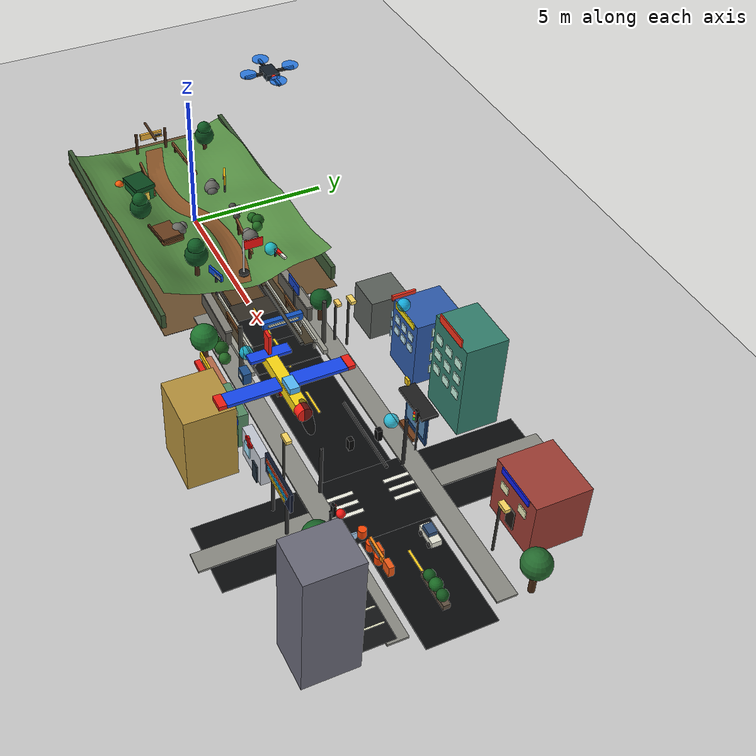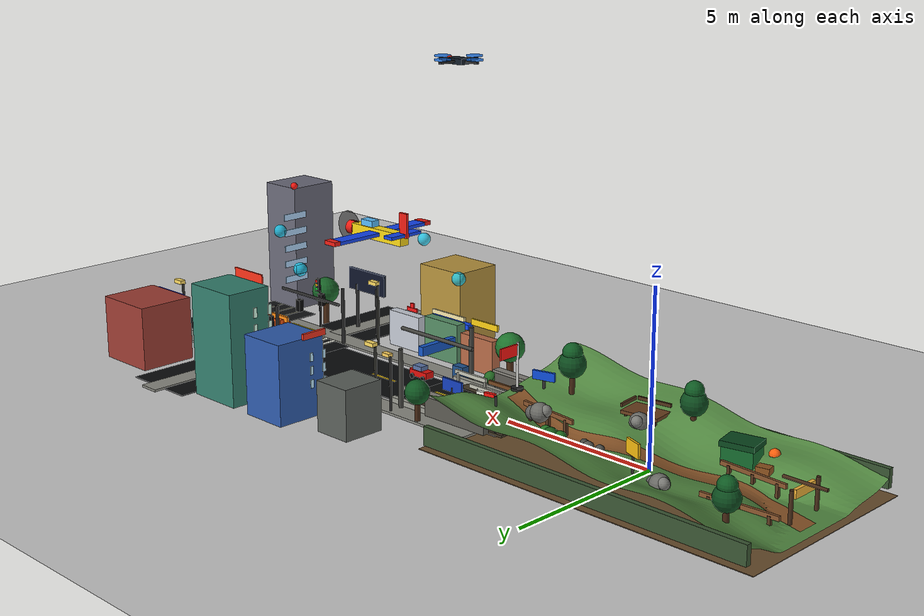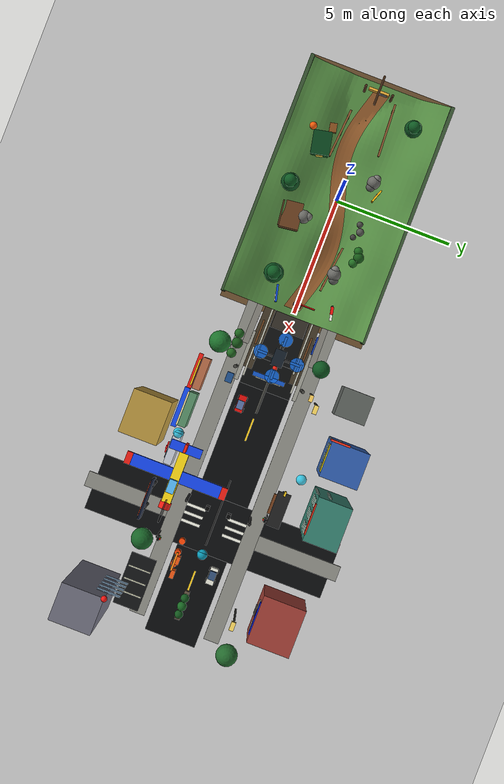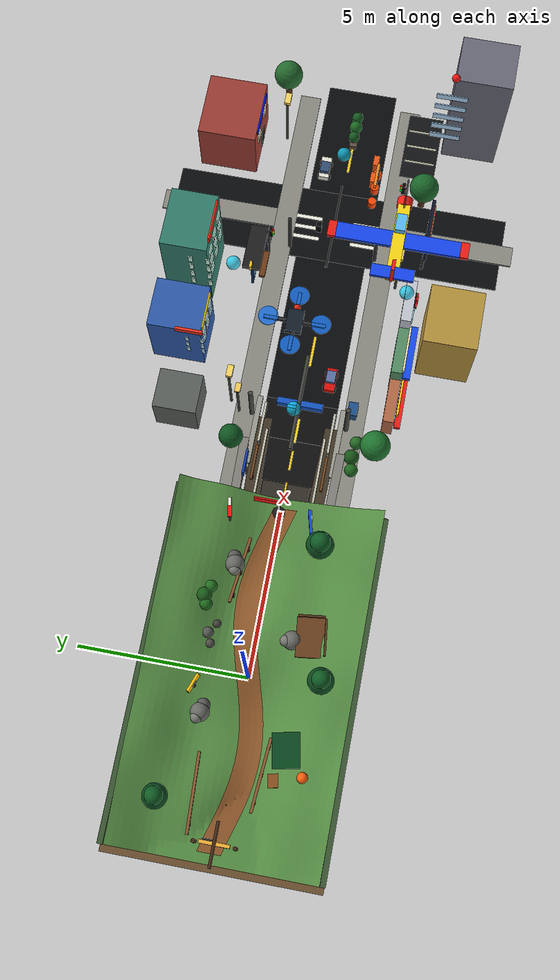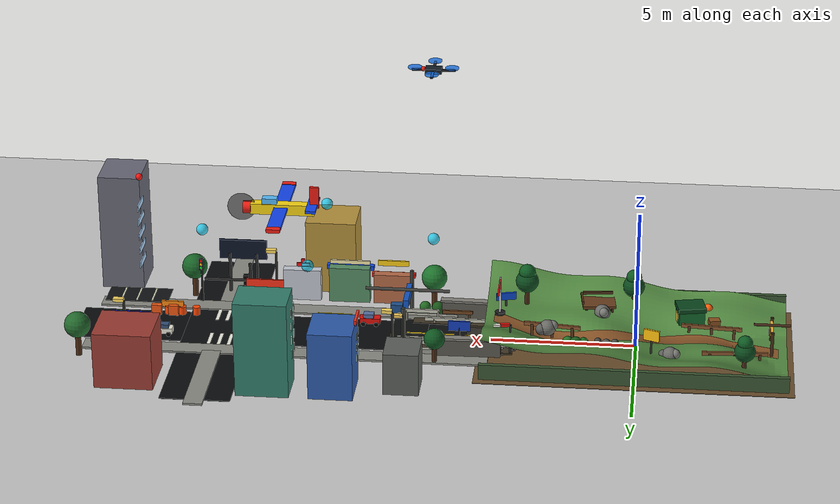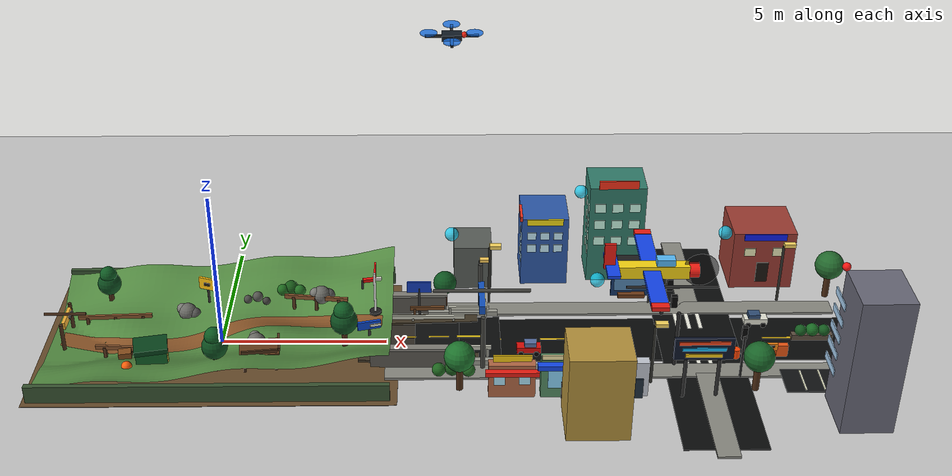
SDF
<?xml version="1.0" ?>
<sdf version="1.6">
  <world name="mountain_city_air_demo">
    <!-- Keep the original conservative physics so the mountain car remains stable. -->
    <physics name="default_physics" type="ode">
      <max_step_size>0.001</max_step_size>
      <real_time_factor>1.0</real_time_factor>
      <real_time_update_rate>1000</real_time_update_rate>
      <ode>
        <solver>
          <type>quick</type>
          <iters>80</iters>
          <sor>1.0</sor>
        </solver>
        <constraints>
          <cfm>0.0</cfm>
          <erp>0.2</erp>
          <contact_max_correcting_vel>1.0</contact_max_correcting_vel>
          <contact_surface_layer>0.001</contact_surface_layer>
        </constraints>
      </ode>
    </physics>

    <scene>
      <ambient>0.48 0.50 0.52 1</ambient>
      <background>0.68 0.82 0.96 1</background>
      <shadows>true</shadows>
    </scene>

    <include>
      <uri>model://sun</uri>
    </include>

    <include>
      <uri>model://ground_plane</uri>
    </include>

    <!-- Original mountain area. -->
    <include>
      <uri>model://mountain_terrain</uri>
      <pose>0 0 0 0 0 0</pose>
    </include>

    <include>
      <name>rock_obstacle_left</name>
      <uri>model://rock_obstacle</uri>
      <pose>-1.2 1.15 0.18 0 0 0.35</pose>
    </include>

    <include>
      <name>rock_obstacle_right</name>
      <uri>model://rock_obstacle</uri>
      <pose>1.2 -1.05 0.58 0 0 -0.55</pose>
    </include>

    <include>
      <name>rock_obstacle_top</name>
      <uri>model://rock_obstacle</uri>
      <pose>3.0 0.95 0.92 0 0 0.85</pose>
    </include>

    <include>
      <uri>model://checkpoint_flag</uri>
      <pose>4.7 0.0 1.05 0 0 0</pose>
    </include>

    <!-- Decorative mountain layer: guard rails, signs, lookout platform, camp and vegetation. -->
    <include>
      <name>mountain_showcase_details</name>
      <uri>model://mountain_showcase_details</uri>
      <pose>0 0 0 0 0 0</pose>
    </include>

    <!-- Blended transition from mountain trail to city street. -->
    <include>
      <name>mountain_city_transition</name>
      <uri>model://mountain_city_transition</uri>
      <pose>0 0 0 0 0 0</pose>
    </include>

    <!-- New city block: roads, buildings, sidewalks, lights, trees and signs. -->
    <include>
      <name>simple_city</name>
      <uri>model://simple_city</uri>
      <pose>0 0 0 0 0 0</pose>
    </include>

    <!-- Camera-facing city details: storefronts, billboard, gantry, parking and flight markers. -->
    <include>
      <name>showcase_city_details</name>
      <uri>model://showcase_city_details</uri>
      <pose>0 0 0 0 0 0</pose>
    </include>

    <!-- Lightweight UAV kept as a secondary aerial object. -->
    <include>
      <name>city_patrol_drone</name>
      <uri>model://simple_drone</uri>
      <pose>7.0 0.0 10.0 0 0 0</pose>
    </include>

    <!-- Larger fixed-wing aircraft for an obvious answer-defense visual. -->
    <include>
      <name>patrol_airplane</name>
      <uri>model://simple_airplane</uri>
      <pose>12.5 -2.0 3.8 0 0 0</pose>
    </include>

    <!-- Camera sees the mountain, transition road, city details and the low-aircraft path. -->
    <gui fullscreen="0">
      <camera name="user_camera">
        <pose>7.2 -17.5 8.4 0 0.44 0.44</pose>
        <view_controller>orbit</view_controller>
      </camera>
    </gui>
  </world>
</sdf>

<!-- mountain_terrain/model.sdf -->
<sdf version="1.6">
  <model name="mountain_terrain">
    <static>true</static>

    <!--
      山地主体使用程序化网格 mesh，而不是少量 box。
      mesh 中包含主坡度、两侧山脊、中央蛇形车道和小幅起伏，展示效果更接近山地。
    -->
    <link name="terrain_mesh">
      <pose>0 0 0 0 0 0</pose>
      <collision name="collision">
        <geometry>
          <mesh>
            <uri>model://mountain_terrain/meshes/mountain_terrain.dae</uri>
          </mesh>
        </geometry>
        <surface>
          <friction>
            <ode>
              <mu>2.0</mu>
              <mu2>2.0</mu2>
            </ode>
          </friction>
          <contact>
            <ode>
              <kp>100000</kp>
              <kd>1.0</kd>
            </ode>
          </contact>
        </surface>
      </collision>
      <visual name="visual">
        <geometry>
          <mesh>
            <uri>model://mountain_terrain/meshes/mountain_terrain.dae</uri>
          </mesh>
        </geometry>
        <material>
          <ambient>0.23 0.38 0.20 1</ambient>
          <diffuse>0.33 0.55 0.26 1</diffuse>
          <specular>0.04 0.04 0.03 1</specular>
        </material>
      </visual>
    </link>

    <!-- 贴合 mesh 高度的蛇形土路，只作为视觉层，帮助展示山地路线。 -->
    <link name="trail_visual">
      <pose>0 0 0 0 0 0</pose>
      <visual name="visual">
        <geometry>
          <mesh>
            <uri>model://mountain_terrain/meshes/mountain_trail.dae</uri>
          </mesh>
        </geometry>
        <material>
          <ambient>0.36 0.22 0.10 1</ambient>
          <diffuse>0.55 0.34 0.16 1</diffuse>
        </material>
      </visual>
    </link>

    <!-- 山地外圈土色底座，帮助从 Gazebo 网格背景中区分实验场地范围。 -->
    <link name="terrain_base">
      <pose>0 0 -0.035 0 0 0</pose>
      <collision name="collision">
        <geometry>
          <box>
            <size>10.8 6.3 0.05</size>
          </box>
        </geometry>
      </collision>
      <visual name="visual">
        <geometry>
          <box>
            <size>10.8 6.3 0.05</size>
          </box>
        </geometry>
        <material>
          <ambient>0.28 0.20 0.12 1</ambient>
          <diffuse>0.42 0.31 0.18 1</diffuse>
        </material>
      </visual>
    </link>

    <!-- 两侧低矮护栏用于强调山路边界，也避免小车演示时跑出场景。 -->
    <link name="left_boundary">
      <pose>0 3.08 0.42 0 0 0</pose>
      <collision name="collision">
        <geometry>
          <box>
            <size>10.4 0.16 0.55</size>
          </box>
        </geometry>
      </collision>
      <visual name="visual">
        <geometry>
          <box>
            <size>10.4 0.16 0.55</size>
          </box>
        </geometry>
        <material>
          <ambient>0.18 0.25 0.15 1</ambient>
          <diffuse>0.23 0.34 0.20 1</diffuse>
        </material>
      </visual>
    </link>

    <link name="right_boundary">
      <pose>0 -3.08 0.42 0 0 0</pose>
      <collision name="collision">
        <geometry>
          <box>
            <size>10.4 0.16 0.55</size>
          </box>
        </geometry>
      </collision>
      <visual name="visual">
        <geometry>
          <box>
            <size>10.4 0.16 0.55</size>
          </box>
        </geometry>
        <material>
          <ambient>0.18 0.25 0.15 1</ambient>
          <diffuse>0.23 0.34 0.20 1</diffuse>
        </material>
      </visual>
    </link>
  </model>
</sdf>

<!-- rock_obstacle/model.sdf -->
<sdf version="1.6">
  <model name="rock_obstacle">
    <static>true</static>

    <!-- 由多个球体拼成不规则岩石，避免依赖外部 mesh。 -->
    <link name="rock_cluster">
      <collision name="main_collision">
        <pose>0 0 0.16 0 0 0</pose>
        <geometry>
          <sphere>
            <radius>0.28</radius>
          </sphere>
        </geometry>
      </collision>
      <visual name="main_visual">
        <pose>0 0 0.16 0 0 0</pose>
        <geometry>
          <sphere>
            <radius>0.28</radius>
          </sphere>
        </geometry>
        <material>
          <ambient>0.26 0.26 0.25 1</ambient>
          <diffuse>0.42 0.42 0.40 1</diffuse>
        </material>
      </visual>

      <collision name="side_collision">
        <pose>0.18 -0.12 0.12 0 0 0</pose>
        <geometry>
          <sphere>
            <radius>0.20</radius>
          </sphere>
        </geometry>
      </collision>
      <visual name="side_visual">
        <pose>0.18 -0.12 0.12 0 0 0</pose>
        <geometry>
          <sphere>
            <radius>0.20</radius>
          </sphere>
        </geometry>
        <material>
          <ambient>0.22 0.22 0.22 1</ambient>
          <diffuse>0.36 0.36 0.35 1</diffuse>
        </material>
      </visual>

      <collision name="cap_collision">
        <pose>-0.14 0.12 0.24 0 0 0</pose>
        <geometry>
          <sphere>
            <radius>0.17</radius>
          </sphere>
        </geometry>
      </collision>
      <visual name="cap_visual">
        <pose>-0.14 0.12 0.24 0 0 0</pose>
        <geometry>
          <sphere>
            <radius>0.17</radius>
          </sphere>
        </geometry>
        <material>
          <ambient>0.30 0.30 0.29 1</ambient>
          <diffuse>0.48 0.48 0.46 1</diffuse>
        </material>
      </visual>
    </link>
  </model>
</sdf>

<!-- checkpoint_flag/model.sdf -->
<sdf version="1.6">
  <model name="checkpoint_flag">
    <static>true</static>

    <link name="flag_link">
      <!-- 旗杆底座，提高视觉稳定感。 -->
      <collision name="base_collision">
        <pose>0 0 0.04 0 0 0</pose>
        <geometry>
          <cylinder>
            <radius>0.18</radius>
            <length>0.08</length>
          </cylinder>
        </geometry>
      </collision>
      <visual name="base_visual">
        <pose>0 0 0.04 0 0 0</pose>
        <geometry>
          <cylinder>
            <radius>0.18</radius>
            <length>0.08</length>
          </cylinder>
        </geometry>
        <material>
          <ambient>0.08 0.08 0.08 1</ambient>
          <diffuse>0.12 0.12 0.12 1</diffuse>
        </material>
      </visual>

      <collision name="pole_collision">
        <pose>0 0 0.72 0 0 0</pose>
        <geometry>
          <cylinder>
            <radius>0.035</radius>
            <length>1.36</length>
          </cylinder>
        </geometry>
      </collision>
      <visual name="pole_visual">
        <pose>0 0 0.72 0 0 0</pose>
        <geometry>
          <cylinder>
            <radius>0.035</radius>
            <length>1.36</length>
          </cylinder>
        </geometry>
        <material>
          <ambient>0.78 0.78 0.78 1</ambient>
          <diffuse>0.90 0.90 0.88 1</diffuse>
        </material>
      </visual>

      <!-- 红色旗面用于标识终点检查点。 -->
      <collision name="flag_collision">
        <pose>0 0.35 1.18 0 0 0</pose>
        <geometry>
          <box>
            <size>0.04 0.70 0.34</size>
          </box>
        </geometry>
      </collision>
      <visual name="flag_visual">
        <pose>0 0.35 1.18 0 0 0</pose>
        <geometry>
          <box>
            <size>0.04 0.70 0.34</size>
          </box>
        </geometry>
        <material>
          <ambient>0.85 0.06 0.05 1</ambient>
          <diffuse>1.00 0.08 0.06 1</diffuse>
        </material>
      </visual>
    </link>
  </model>
</sdf>

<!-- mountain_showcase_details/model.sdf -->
<sdf version="1.6">
  <model name="mountain_showcase_details">
    <static>true</static>

    <!-- Mountain-road guard rails near the start and the city connector. -->
    <link name="trail_guard_rail_start_north">
      <pose>-3.4 0.88 0.36 0 0 0.05</pose>
      <visual name="rail"><geometry><box><size>2.25 0.08 0.13</size></box></geometry><material><ambient>0.55 0.34 0.18 1</ambient><diffuse>0.55 0.34 0.18 1</diffuse></material></visual>
      <visual name="post_1"><pose>-0.85 0 -0.22 0 0 0</pose><geometry><box><size>0.09 0.09 0.44</size></box></geometry><material><ambient>0.35 0.22 0.12 1</ambient><diffuse>0.35 0.22 0.12 1</diffuse></material></visual>
      <visual name="post_2"><pose>0 0 -0.22 0 0 0</pose><geometry><box><size>0.09 0.09 0.44</size></box></geometry><material><ambient>0.35 0.22 0.12 1</ambient><diffuse>0.35 0.22 0.12 1</diffuse></material></visual>
      <visual name="post_3"><pose>0.85 0 -0.22 0 0 0</pose><geometry><box><size>0.09 0.09 0.44</size></box></geometry><material><ambient>0.35 0.22 0.12 1</ambient><diffuse>0.35 0.22 0.12 1</diffuse></material></visual>
    </link>

    <link name="trail_guard_rail_start_south">
      <pose>-2.6 -0.88 0.42 0 0 -0.08</pose>
      <visual name="rail"><geometry><box><size>2.10 0.08 0.13</size></box></geometry><material><ambient>0.55 0.34 0.18 1</ambient><diffuse>0.55 0.34 0.18 1</diffuse></material></visual>
      <visual name="post_1"><pose>-0.78 0 -0.23 0 0 0</pose><geometry><box><size>0.09 0.09 0.46</size></box></geometry><material><ambient>0.35 0.22 0.12 1</ambient><diffuse>0.35 0.22 0.12 1</diffuse></material></visual>
      <visual name="post_2"><pose>0 0 -0.23 0 0 0</pose><geometry><box><size>0.09 0.09 0.46</size></box></geometry><material><ambient>0.35 0.22 0.12 1</ambient><diffuse>0.35 0.22 0.12 1</diffuse></material></visual>
      <visual name="post_3"><pose>0.78 0 -0.23 0 0 0</pose><geometry><box><size>0.09 0.09 0.46</size></box></geometry><material><ambient>0.35 0.22 0.12 1</ambient><diffuse>0.35 0.22 0.12 1</diffuse></material></visual>
    </link>

    <link name="trail_guard_rail_top">
      <pose>2.85 0.78 1.08 0 0 -0.12</pose>
      <visual name="rail"><geometry><box><size>1.95 0.08 0.13</size></box></geometry><material><ambient>0.55 0.34 0.18 1</ambient><diffuse>0.55 0.34 0.18 1</diffuse></material></visual>
      <visual name="post_1"><pose>-0.70 0 -0.22 0 0 0</pose><geometry><box><size>0.09 0.09 0.44</size></box></geometry><material><ambient>0.35 0.22 0.12 1</ambient><diffuse>0.35 0.22 0.12 1</diffuse></material></visual>
      <visual name="post_2"><pose>0 0 -0.22 0 0 0</pose><geometry><box><size>0.09 0.09 0.44</size></box></geometry><material><ambient>0.35 0.22 0.12 1</ambient><diffuse>0.35 0.22 0.12 1</diffuse></material></visual>
      <visual name="post_3"><pose>0.70 0 -0.22 0 0 0</pose><geometry><box><size>0.09 0.09 0.44</size></box></geometry><material><ambient>0.35 0.22 0.12 1</ambient><diffuse>0.35 0.22 0.12 1</diffuse></material></visual>
    </link>

    <!-- Trailhead gate and mountain direction signs. -->
    <link name="trailhead_gate">
      <pose>-4.65 0 0.18 0 0 0</pose>
      <visual name="left_post"><pose>0 0.58 0.44 0 0 0</pose><geometry><cylinder><radius>0.055</radius><length>0.88</length></cylinder></geometry><material><ambient>0.28 0.17 0.09 1</ambient><diffuse>0.28 0.17 0.09 1</diffuse></material></visual>
      <visual name="right_post"><pose>0 -0.58 0.44 0 0 0</pose><geometry><cylinder><radius>0.055</radius><length>0.88</length></cylinder></geometry><material><ambient>0.28 0.17 0.09 1</ambient><diffuse>0.28 0.17 0.09 1</diffuse></material></visual>
      <visual name="top_beam"><pose>0 0 0.88 0 1.5708 0</pose><geometry><cylinder><radius>0.045</radius><length>1.25</length></cylinder></geometry><material><ambient>0.28 0.17 0.09 1</ambient><diffuse>0.28 0.17 0.09 1</diffuse></material></visual>
      <visual name="sign_board"><pose>0.02 0 0.72 0 0 0</pose><geometry><box><size>0.10 0.86 0.24</size></box></geometry><material><ambient>0.95 0.70 0.22 1</ambient><diffuse>0.95 0.70 0.22 1</diffuse></material></visual>
      <visual name="arrow"><pose>0.08 0.20 0.72 0 0 0</pose><geometry><box><size>0.08 0.34 0.08</size></box></geometry><material><ambient>0.08 0.08 0.08 1</ambient><diffuse>0.08 0.08 0.08 1</diffuse></material></visual>
    </link>

    <link name="warning_sign_rocks">
      <pose>-0.55 1.42 0.52 0 0 -0.35</pose>
      <visual name="pole"><pose>0 0 0.28 0 0 0</pose><geometry><cylinder><radius>0.035</radius><length>0.56</length></cylinder></geometry><material><ambient>0.20 0.20 0.18 1</ambient><diffuse>0.20 0.20 0.18 1</diffuse></material></visual>
      <visual name="triangle_base"><pose>0 0 0.68 0 0 0</pose><geometry><box><size>0.56 0.07 0.40</size></box></geometry><material><ambient>1.0 0.76 0.06 1</ambient><diffuse>1.0 0.76 0.06 1</diffuse></material></visual>
      <visual name="symbol"><pose>0 -0.04 0.68 0 0 0</pose><geometry><box><size>0.20 0.04 0.10</size></box></geometry><material><ambient>0.10 0.08 0.04 1</ambient><diffuse>0.10 0.08 0.04 1</diffuse></material></visual>
    </link>

    <link name="city_direction_sign">
      <pose>4.55 -0.95 1.08 0 0 0.25</pose>
      <visual name="pole"><pose>0 0 -0.30 0 0 0</pose><geometry><cylinder><radius>0.04</radius><length>0.86</length></cylinder></geometry><material><ambient>0.20 0.20 0.20 1</ambient><diffuse>0.20 0.20 0.20 1</diffuse></material></visual>
      <visual name="board"><pose>0 0 0.18 0 0 0</pose><geometry><box><size>0.70 0.08 0.26</size></box></geometry><material><ambient>0.05 0.30 0.85 1</ambient><diffuse>0.05 0.30 0.85 1</diffuse></material></visual>
      <visual name="arrow"><pose>0.18 -0.05 0.18 0 0 0</pose><geometry><box><size>0.32 0.04 0.08</size></box></geometry><material><ambient>0.96 0.96 0.88 1</ambient><diffuse>0.96 0.96 0.88 1</diffuse></material></visual>
    </link>

    <!-- Scenic lookout and small camp make the mountain feel inhabited. -->
    <link name="lookout_platform">
      <pose>1.35 -1.55 0.86 0 0 0.12</pose>
      <visual name="deck"><geometry><box><size>1.15 0.82 0.10</size></box></geometry><material><ambient>0.42 0.25 0.12 1</ambient><diffuse>0.42 0.25 0.12 1</diffuse></material></visual>
      <visual name="post_1"><pose>-0.45 -0.32 -0.28 0 0 0</pose><geometry><box><size>0.08 0.08 0.56</size></box></geometry><material><ambient>0.26 0.16 0.09 1</ambient><diffuse>0.26 0.16 0.09 1</diffuse></material></visual>
      <visual name="post_2"><pose>0.45 -0.32 -0.28 0 0 0</pose><geometry><box><size>0.08 0.08 0.56</size></box></geometry><material><ambient>0.26 0.16 0.09 1</ambient><diffuse>0.26 0.16 0.09 1</diffuse></material></visual>
      <visual name="post_3"><pose>-0.45 0.32 -0.28 0 0 0</pose><geometry><box><size>0.08 0.08 0.56</size></box></geometry><material><ambient>0.26 0.16 0.09 1</ambient><diffuse>0.26 0.16 0.09 1</diffuse></material></visual>
      <visual name="post_4"><pose>0.45 0.32 -0.28 0 0 0</pose><geometry><box><size>0.08 0.08 0.56</size></box></geometry><material><ambient>0.26 0.16 0.09 1</ambient><diffuse>0.26 0.16 0.09 1</diffuse></material></visual>
      <visual name="front_rail"><pose>0 -0.42 0.18 0 0 0</pose><geometry><box><size>1.05 0.06 0.10</size></box></geometry><material><ambient>0.32 0.20 0.10 1</ambient><diffuse>0.32 0.20 0.10 1</diffuse></material></visual>
      <visual name="side_rail"><pose>0.58 0 0.18 0 0 0</pose><geometry><box><size>0.06 0.76 0.10</size></box></geometry><material><ambient>0.32 0.20 0.10 1</ambient><diffuse>0.32 0.20 0.10 1</diffuse></material></visual>
    </link>

    <link name="mountain_camp">
      <pose>-1.85 -1.45 0.36 0 0 0.20</pose>
      <visual name="tent_body"><pose>0 0 0.24 0 0 0</pose><geometry><box><size>0.90 0.70 0.48</size></box></geometry><material><ambient>0.08 0.42 0.18 1</ambient><diffuse>0.08 0.42 0.18 1</diffuse></material></visual>
      <visual name="tent_roof"><pose>0 0 0.55 0 0 0</pose><geometry><box><size>0.98 0.78 0.16</size></box></geometry><material><ambient>0.04 0.28 0.12 1</ambient><diffuse>0.04 0.28 0.12 1</diffuse></material></visual>
      <visual name="door"><pose>0.46 0 0.18 0 0 0</pose><geometry><box><size>0.04 0.30 0.34</size></box></geometry><material><ambient>0.95 0.82 0.30 1</ambient><diffuse>0.95 0.82 0.30 1</diffuse></material></visual>
      <visual name="supply_box"><pose>-0.78 0.38 0.10 0 0 0</pose><geometry><box><size>0.38 0.30 0.20</size></box></geometry><material><ambient>0.55 0.32 0.12 1</ambient><diffuse>0.55 0.32 0.12 1</diffuse></material></visual>
      <visual name="campfire_base"><pose>-0.72 -0.44 0.06 0 0 0</pose><geometry><cylinder><radius>0.22</radius><length>0.08</length></cylinder></geometry><material><ambient>0.18 0.12 0.08 1</ambient><diffuse>0.18 0.12 0.08 1</diffuse></material></visual>
      <visual name="campfire_flame"><pose>-0.72 -0.44 0.22 0 0 0</pose><geometry><sphere><radius>0.16</radius></sphere></geometry><material><ambient>1.0 0.38 0.05 1</ambient><diffuse>1.0 0.38 0.05 1</diffuse></material></visual>
    </link>

    <!-- Vegetation and small stones around the mountain road. -->
    <link name="pine_tree_1">
      <pose>-3.7 1.85 0.18 0 0 0</pose>
      <visual name="trunk"><pose>0 0 0.32 0 0 0</pose><geometry><cylinder><radius>0.08</radius><length>0.64</length></cylinder></geometry><material><ambient>0.28 0.16 0.08 1</ambient><diffuse>0.28 0.16 0.08 1</diffuse></material></visual>
      <visual name="crown_low"><pose>0 0 0.78 0 0 0</pose><geometry><sphere><radius>0.36</radius></sphere></geometry><material><ambient>0.05 0.30 0.12 1</ambient><diffuse>0.05 0.30 0.12 1</diffuse></material></visual>
      <visual name="crown_top"><pose>0 0 1.10 0 0 0</pose><geometry><sphere><radius>0.26</radius></sphere></geometry><material><ambient>0.06 0.36 0.14 1</ambient><diffuse>0.06 0.36 0.14 1</diffuse></material></visual>
    </link>

    <link name="pine_tree_2">
      <pose>0.15 -2.05 0.48 0 0 0</pose>
      <visual name="trunk"><pose>0 0 0.34 0 0 0</pose><geometry><cylinder><radius>0.08</radius><length>0.68</length></cylinder></geometry><material><ambient>0.28 0.16 0.08 1</ambient><diffuse>0.28 0.16 0.08 1</diffuse></material></visual>
      <visual name="crown_low"><pose>0 0 0.83 0 0 0</pose><geometry><sphere><radius>0.38</radius></sphere></geometry><material><ambient>0.05 0.30 0.12 1</ambient><diffuse>0.05 0.30 0.12 1</diffuse></material></visual>
      <visual name="crown_top"><pose>0 0 1.18 0 0 0</pose><geometry><sphere><radius>0.27</radius></sphere></geometry><material><ambient>0.06 0.36 0.14 1</ambient><diffuse>0.06 0.36 0.14 1</diffuse></material></visual>
    </link>

    <link name="pine_tree_3">
      <pose>3.85 -1.35 0.78 0 0 0</pose>
      <visual name="trunk"><pose>0 0 0.36 0 0 0</pose><geometry><cylinder><radius>0.08</radius><length>0.72</length></cylinder></geometry><material><ambient>0.28 0.16 0.08 1</ambient><diffuse>0.28 0.16 0.08 1</diffuse></material></visual>
      <visual name="crown_low"><pose>0 0 0.90 0 0 0</pose><geometry><sphere><radius>0.40</radius></sphere></geometry><material><ambient>0.05 0.30 0.12 1</ambient><diffuse>0.05 0.30 0.12 1</diffuse></material></visual>
      <visual name="crown_top"><pose>0 0 1.24 0 0 0</pose><geometry><sphere><radius>0.29</radius></sphere></geometry><material><ambient>0.06 0.36 0.14 1</ambient><diffuse>0.06 0.36 0.14 1</diffuse></material></visual>
    </link>

    <link name="shrub_cluster">
      <pose>2.0 1.55 0.78 0 0 0</pose>
      <visual name="bush_1"><pose>-0.25 0 0.10 0 0 0</pose><geometry><sphere><radius>0.18</radius></sphere></geometry><material><ambient>0.12 0.42 0.12 1</ambient><diffuse>0.12 0.42 0.12 1</diffuse></material></visual>
      <visual name="bush_2"><pose>0.00 0.10 0.12 0 0 0</pose><geometry><sphere><radius>0.22</radius></sphere></geometry><material><ambient>0.10 0.36 0.10 1</ambient><diffuse>0.10 0.36 0.10 1</diffuse></material></visual>
      <visual name="bush_3"><pose>0.28 -0.04 0.10 0 0 0</pose><geometry><sphere><radius>0.18</radius></sphere></geometry><material><ambient>0.14 0.44 0.14 1</ambient><diffuse>0.14 0.44 0.14 1</diffuse></material></visual>
    </link>

    <link name="loose_rocks">
      <pose>0.95 1.22 0.68 0 0 0</pose>
      <visual name="stone_1"><pose>-0.26 0 0.07 0 0 0</pose><geometry><sphere><radius>0.13</radius></sphere></geometry><material><ambient>0.30 0.30 0.28 1</ambient><diffuse>0.30 0.30 0.28 1</diffuse></material></visual>
      <visual name="stone_2"><pose>0.03 0.12 0.09 0 0 0</pose><geometry><sphere><radius>0.16</radius></sphere></geometry><material><ambient>0.34 0.34 0.32 1</ambient><diffuse>0.34 0.34 0.32 1</diffuse></material></visual>
      <visual name="stone_3"><pose>0.32 -0.08 0.06 0 0 0</pose><geometry><sphere><radius>0.12</radius></sphere></geometry><material><ambient>0.26 0.26 0.24 1</ambient><diffuse>0.26 0.26 0.24 1</diffuse></material></visual>
    </link>

    <!-- A small wind sock helps show wind/air theme next to the mountain route. -->
    <link name="mountain_windsock">
      <pose>4.25 1.35 1.15 0 0 0.2</pose>
      <visual name="pole"><pose>0 0 -0.35 0 0 0</pose><geometry><cylinder><radius>0.035</radius><length>1.05</length></cylinder></geometry><material><ambient>0.20 0.20 0.20 1</ambient><diffuse>0.20 0.20 0.20 1</diffuse></material></visual>
      <visual name="sock_red"><pose>0.18 0 0.18 0 0 0</pose><geometry><box><size>0.32 0.12 0.10</size></box></geometry><material><ambient>0.95 0.08 0.05 1</ambient><diffuse>0.95 0.08 0.05 1</diffuse></material></visual>
      <visual name="sock_white"><pose>0.46 0 0.18 0 0 0</pose><geometry><box><size>0.26 0.10 0.08</size></box></geometry><material><ambient>0.95 0.95 0.90 1</ambient><diffuse>0.95 0.95 0.90 1</diffuse></material></visual>
    </link>
  </model>
</sdf>

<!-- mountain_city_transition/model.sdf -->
<sdf version="1.6">
  <model name="mountain_city_transition">
    <static>true</static>

    <!-- Layered road surface: dirt trail fades into a wider asphalt city entry. -->
    <link name="dirt_exit_patch">
      <pose>4.85 0 0.075 0 0 0</pose>
      <collision name="collision"><geometry><box><size>1.80 1.22 0.035</size></box></geometry></collision>
      <visual name="visual">
        <geometry><box><size>1.80 1.22 0.035</size></box></geometry>
        <material><ambient>0.34 0.24 0.13 1</ambient><diffuse>0.34 0.24 0.13 1</diffuse></material>
      </visual>
    </link>

    <link name="mixed_gravel_patch">
      <pose>5.85 0 0.085 0 0 0</pose>
      <collision name="collision"><geometry><box><size>1.65 1.42 0.035</size></box></geometry></collision>
      <visual name="visual">
        <geometry><box><size>1.65 1.42 0.035</size></box></geometry>
        <material><ambient>0.20 0.18 0.15 1</ambient><diffuse>0.20 0.18 0.15 1</diffuse></material>
      </visual>
    </link>

    <link name="asphalt_entry_patch">
      <pose>6.95 0 0.095 0 0 0</pose>
      <collision name="collision"><geometry><box><size>2.15 1.72 0.038</size></box></geometry></collision>
      <visual name="visual">
        <geometry><box><size>2.15 1.72 0.038</size></box></geometry>
        <material><ambient>0.055 0.058 0.060 1</ambient><diffuse>0.055 0.058 0.060 1</diffuse></material>
      </visual>
    </link>

    <link name="city_entry_flare">
      <pose>7.85 0 0.105 0 0 0</pose>
      <collision name="collision"><geometry><box><size>1.25 2.18 0.035</size></box></geometry></collision>
      <visual name="visual">
        <geometry><box><size>1.25 2.18 0.035</size></box></geometry>
        <material><ambient>0.045 0.048 0.050 1</ambient><diffuse>0.045 0.048 0.050 1</diffuse></material>
      </visual>
    </link>

    <!-- Shoulders hide the hard seam between the mountain mesh and the city road. -->
    <link name="north_earth_shoulder">
      <pose>6.00 1.00 0.11 0 0 0.03</pose>
      <visual name="visual">
        <geometry><box><size>3.60 0.46 0.07</size></box></geometry>
        <material><ambient>0.26 0.22 0.15 1</ambient><diffuse>0.26 0.22 0.15 1</diffuse></material>
      </visual>
    </link>

    <link name="south_earth_shoulder">
      <pose>6.00 -1.00 0.11 0 0 -0.03</pose>
      <visual name="visual">
        <geometry><box><size>3.60 0.46 0.07</size></box></geometry>
        <material><ambient>0.26 0.22 0.15 1</ambient><diffuse>0.26 0.22 0.15 1</diffuse></material>
      </visual>
    </link>

    <link name="north_city_curb">
      <pose>7.35 1.28 0.16 0 0 0</pose>
      <collision name="collision"><geometry><box><size>2.15 0.16 0.16</size></box></geometry></collision>
      <visual name="visual">
        <geometry><box><size>2.15 0.16 0.16</size></box></geometry>
        <material><ambient>0.62 0.62 0.58 1</ambient><diffuse>0.62 0.62 0.58 1</diffuse></material>
      </visual>
    </link>

    <link name="south_city_curb">
      <pose>7.35 -1.28 0.16 0 0 0</pose>
      <collision name="collision"><geometry><box><size>2.15 0.16 0.16</size></box></geometry></collision>
      <visual name="visual">
        <geometry><box><size>2.15 0.16 0.16</size></box></geometry>
        <material><ambient>0.62 0.62 0.58 1</ambient><diffuse>0.62 0.62 0.58 1</diffuse></material>
      </visual>
    </link>

    <!-- Retaining walls and mixed guard rails bridge the visual language of mountain and city. -->
    <link name="north_retaining_wall">
      <pose>5.70 1.42 0.42 0 0 0.02</pose>
      <collision name="collision"><geometry><box><size>2.25 0.20 0.58</size></box></geometry></collision>
      <visual name="wall">
        <geometry><box><size>2.25 0.20 0.58</size></box></geometry>
        <material><ambient>0.36 0.35 0.32 1</ambient><diffuse>0.36 0.35 0.32 1</diffuse></material>
      </visual>
      <visual name="cap"><pose>0 0 0.34 0 0 0</pose><geometry><box><size>2.35 0.26 0.08</size></box></geometry><material><ambient>0.52 0.51 0.48 1</ambient><diffuse>0.52 0.51 0.48 1</diffuse></material></visual>
    </link>

    <link name="south_retaining_wall">
      <pose>5.70 -1.42 0.42 0 0 -0.02</pose>
      <collision name="collision"><geometry><box><size>2.25 0.20 0.58</size></box></geometry></collision>
      <visual name="wall">
        <geometry><box><size>2.25 0.20 0.58</size></box></geometry>
        <material><ambient>0.36 0.35 0.32 1</ambient><diffuse>0.36 0.35 0.32 1</diffuse></material>
      </visual>
      <visual name="cap"><pose>0 0 0.34 0 0 0</pose><geometry><box><size>2.35 0.26 0.08</size></box></geometry><material><ambient>0.52 0.51 0.48 1</ambient><diffuse>0.52 0.51 0.48 1</diffuse></material></visual>
    </link>

    <link name="north_wood_to_metal_rail">
      <pose>6.95 1.05 0.50 0 0 0</pose>
      <visual name="wood_part"><pose>-0.70 0 0 0 0 0</pose><geometry><box><size>1.05 0.07 0.12</size></box></geometry><material><ambient>0.46 0.28 0.13 1</ambient><diffuse>0.46 0.28 0.13 1</diffuse></material></visual>
      <visual name="metal_part"><pose>0.58 0 0 0 0 0</pose><geometry><box><size>1.25 0.07 0.12</size></box></geometry><material><ambient>0.78 0.78 0.72 1</ambient><diffuse>0.78 0.78 0.72 1</diffuse></material></visual>
      <visual name="post_1"><pose>-1.10 0 -0.24 0 0 0</pose><geometry><box><size>0.07 0.07 0.48</size></box></geometry><material><ambient>0.38 0.24 0.12 1</ambient><diffuse>0.38 0.24 0.12 1</diffuse></material></visual>
      <visual name="post_2"><pose>0.00 0 -0.24 0 0 0</pose><geometry><box><size>0.07 0.07 0.48</size></box></geometry><material><ambient>0.58 0.58 0.54 1</ambient><diffuse>0.58 0.58 0.54 1</diffuse></material></visual>
      <visual name="post_3"><pose>1.10 0 -0.24 0 0 0</pose><geometry><box><size>0.07 0.07 0.48</size></box></geometry><material><ambient>0.58 0.58 0.54 1</ambient><diffuse>0.58 0.58 0.54 1</diffuse></material></visual>
    </link>

    <link name="south_wood_to_metal_rail">
      <pose>6.95 -1.05 0.50 0 0 0</pose>
      <visual name="wood_part"><pose>-0.70 0 0 0 0 0</pose><geometry><box><size>1.05 0.07 0.12</size></box></geometry><material><ambient>0.46 0.28 0.13 1</ambient><diffuse>0.46 0.28 0.13 1</diffuse></material></visual>
      <visual name="metal_part"><pose>0.58 0 0 0 0 0</pose><geometry><box><size>1.25 0.07 0.12</size></box></geometry><material><ambient>0.78 0.78 0.72 1</ambient><diffuse>0.78 0.78 0.72 1</diffuse></material></visual>
      <visual name="post_1"><pose>-1.10 0 -0.24 0 0 0</pose><geometry><box><size>0.07 0.07 0.48</size></box></geometry><material><ambient>0.38 0.24 0.12 1</ambient><diffuse>0.38 0.24 0.12 1</diffuse></material></visual>
      <visual name="post_2"><pose>0.00 0 -0.24 0 0 0</pose><geometry><box><size>0.07 0.07 0.48</size></box></geometry><material><ambient>0.58 0.58 0.54 1</ambient><diffuse>0.58 0.58 0.54 1</diffuse></material></visual>
      <visual name="post_3"><pose>1.10 0 -0.24 0 0 0</pose><geometry><box><size>0.07 0.07 0.48</size></box></geometry><material><ambient>0.58 0.58 0.54 1</ambient><diffuse>0.58 0.58 0.54 1</diffuse></material></visual>
    </link>

    <!-- Lane markings fade in gradually as the trail becomes city road. -->
    <link name="dashed_center_intro_1">
      <pose>5.70 0 0.145 0 0 0</pose>
      <visual name="visual"><geometry><box><size>0.42 0.06 0.018</size></box></geometry><material><ambient>0.95 0.78 0.12 1</ambient><diffuse>0.95 0.78 0.12 1</diffuse></material></visual>
    </link>

    <link name="dashed_center_intro_2">
      <pose>6.60 0 0.150 0 0 0</pose>
      <visual name="visual"><geometry><box><size>0.62 0.07 0.018</size></box></geometry><material><ambient>0.98 0.82 0.12 1</ambient><diffuse>0.98 0.82 0.12 1</diffuse></material></visual>
    </link>

    <link name="dashed_center_intro_3">
      <pose>7.55 0 0.155 0 0 0</pose>
      <visual name="visual"><geometry><box><size>0.78 0.08 0.018</size></box></geometry><material><ambient>1.00 0.86 0.12 1</ambient><diffuse>1.00 0.86 0.12 1</diffuse></material></visual>
    </link>

    <!-- Gateway element marks the mountain-city boundary without feeling like a hard cut. -->
    <link name="mountain_city_gateway">
      <pose>7.90 0 0 0 0 0</pose>
      <visual name="left_post"><pose>0 1.45 0.92 0 0 0</pose><geometry><cylinder><radius>0.07</radius><length>1.84</length></cylinder></geometry><material><ambient>0.26 0.26 0.24 1</ambient><diffuse>0.26 0.26 0.24 1</diffuse></material></visual>
      <visual name="right_post"><pose>0 -1.45 0.92 0 0 0</pose><geometry><cylinder><radius>0.07</radius><length>1.84</length></cylinder></geometry><material><ambient>0.26 0.26 0.24 1</ambient><diffuse>0.26 0.26 0.24 1</diffuse></material></visual>
      <visual name="top_beam"><pose>0 0 1.82 0 1.5708 0</pose><geometry><cylinder><radius>0.055</radius><length>2.92</length></cylinder></geometry><material><ambient>0.26 0.26 0.24 1</ambient><diffuse>0.26 0.26 0.24 1</diffuse></material></visual>
      <visual name="sign_board"><pose>0 -0.02 1.58 0 0 0</pose><geometry><box><size>0.18 1.35 0.28</size></box></geometry><material><ambient>0.08 0.34 0.78 1</ambient><diffuse>0.08 0.34 0.78 1</diffuse></material></visual>
      <visual name="sign_stripe"><pose>0.10 -0.02 1.58 0 0 0</pose><geometry><box><size>0.05 1.05 0.07</size></box></geometry><material><ambient>0.95 0.95 0.82 1</ambient><diffuse>0.95 0.95 0.82 1</diffuse></material></visual>
    </link>

    <!-- Mixed natural and urban roadside objects. -->
    <link name="transition_pine_and_lamp">
      <pose>7.35 1.85 0 0 0 0</pose>
      <visual name="pine_trunk"><pose>-0.55 0 0.36 0 0 0</pose><geometry><cylinder><radius>0.08</radius><length>0.72</length></cylinder></geometry><material><ambient>0.28 0.16 0.08 1</ambient><diffuse>0.28 0.16 0.08 1</diffuse></material></visual>
      <visual name="pine_crown"><pose>-0.55 0 0.92 0 0 0</pose><geometry><sphere><radius>0.36</radius></sphere></geometry><material><ambient>0.06 0.34 0.13 1</ambient><diffuse>0.06 0.34 0.13 1</diffuse></material></visual>
      <visual name="lamp_pole"><pose>0.55 0 0.86 0 0 0</pose><geometry><cylinder><radius>0.04</radius><length>1.72</length></cylinder></geometry><material><ambient>0.16 0.16 0.16 1</ambient><diffuse>0.16 0.16 0.16 1</diffuse></material></visual>
      <visual name="lamp_head"><pose>0.68 0 1.74 0 0 0</pose><geometry><box><size>0.28 0.16 0.10</size></box></geometry><material><ambient>1.0 0.82 0.36 1</ambient><diffuse>1.0 0.82 0.36 1</diffuse></material></visual>
    </link>

    <link name="transition_bushes_south">
      <pose>7.05 -1.82 0.14 0 0 0</pose>
      <visual name="bush_1"><pose>-0.45 0 0.12 0 0 0</pose><geometry><sphere><radius>0.20</radius></sphere></geometry><material><ambient>0.12 0.40 0.12 1</ambient><diffuse>0.12 0.40 0.12 1</diffuse></material></visual>
      <visual name="bush_2"><pose>-0.05 0.06 0.14 0 0 0</pose><geometry><sphere><radius>0.23</radius></sphere></geometry><material><ambient>0.10 0.34 0.10 1</ambient><diffuse>0.10 0.34 0.10 1</diffuse></material></visual>
      <visual name="bush_3"><pose>0.42 -0.02 0.12 0 0 0</pose><geometry><sphere><radius>0.20</radius></sphere></geometry><material><ambient>0.14 0.42 0.14 1</ambient><diffuse>0.14 0.42 0.14 1</diffuse></material></visual>
    </link>

    <link name="transition_service_box">
      <pose>8.45 -1.55 0.24 0 0 0</pose>
      <visual name="box"><geometry><box><size>0.42 0.28 0.48</size></box></geometry><material><ambient>0.12 0.32 0.56 1</ambient><diffuse>0.12 0.32 0.56 1</diffuse></material></visual>
      <visual name="panel"><pose>0 -0.145 0.04 0 0 0</pose><geometry><box><size>0.28 0.025 0.18</size></box></geometry><material><ambient>0.85 0.90 0.92 1</ambient><diffuse>0.85 0.90 0.92 1</diffuse></material></visual>
    </link>
  </model>
</sdf>

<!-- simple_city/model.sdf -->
<sdf version="1.6">
  <model name="simple_city">
    <static>true</static>

    <!-- Main road linking the mountain exit to the city block. -->
    <link name="main_road">
      <pose>12.0 0 0.012 0 0 0</pose>
      <collision name="collision">
        <geometry><box><size>15.0 2.2 0.024</size></box></geometry>
      </collision>
      <visual name="visual">
        <geometry><box><size>15.0 2.2 0.024</size></box></geometry>
        <material><ambient>0.035 0.038 0.042 1</ambient><diffuse>0.035 0.038 0.042 1</diffuse></material>
      </visual>
    </link>

    <link name="cross_road">
      <pose>14.5 0 0.014 0 0 0</pose>
      <collision name="collision">
        <geometry><box><size>2.4 10.5 0.026</size></box></geometry>
      </collision>
      <visual name="visual">
        <geometry><box><size>2.4 10.5 0.026</size></box></geometry>
        <material><ambient>0.04 0.043 0.047 1</ambient><diffuse>0.04 0.043 0.047 1</diffuse></material>
      </visual>
    </link>

    <link name="connector_road">
      <pose>6.2 0 0.018 0 0 0</pose>
      <collision name="collision">
        <geometry><box><size>4.2 1.5 0.026</size></box></geometry>
      </collision>
      <visual name="visual">
        <geometry><box><size>4.2 1.5 0.026</size></box></geometry>
        <material><ambient>0.08 0.075 0.065 1</ambient><diffuse>0.08 0.075 0.065 1</diffuse></material>
      </visual>
    </link>

    <!-- Sidewalks. -->
    <link name="sidewalk_north">
      <pose>12.0 1.65 0.035 0 0 0</pose>
      <collision name="collision">
        <geometry><box><size>14.0 0.65 0.07</size></box></geometry>
      </collision>
      <visual name="visual">
        <geometry><box><size>14.0 0.65 0.07</size></box></geometry>
        <material><ambient>0.55 0.55 0.52 1</ambient><diffuse>0.55 0.55 0.52 1</diffuse></material>
      </visual>
    </link>

    <link name="sidewalk_south">
      <pose>12.0 -1.65 0.035 0 0 0</pose>
      <collision name="collision">
        <geometry><box><size>14.0 0.65 0.07</size></box></geometry>
      </collision>
      <visual name="visual">
        <geometry><box><size>14.0 0.65 0.07</size></box></geometry>
        <material><ambient>0.55 0.55 0.52 1</ambient><diffuse>0.55 0.55 0.52 1</diffuse></material>
      </visual>
    </link>

    <link name="sidewalk_west">
      <pose>14.5 -3.7 0.035 0 0 0</pose>
      <collision name="collision">
        <geometry><box><size>0.65 3.8 0.07</size></box></geometry>
      </collision>
      <visual name="visual">
        <geometry><box><size>0.65 3.8 0.07</size></box></geometry>
        <material><ambient>0.55 0.55 0.52 1</ambient><diffuse>0.55 0.55 0.52 1</diffuse></material>
      </visual>
    </link>

    <link name="sidewalk_east">
      <pose>14.5 3.7 0.035 0 0 0</pose>
      <collision name="collision">
        <geometry><box><size>0.65 3.8 0.07</size></box></geometry>
      </collision>
      <visual name="visual">
        <geometry><box><size>0.65 3.8 0.07</size></box></geometry>
        <material><ambient>0.55 0.55 0.52 1</ambient><diffuse>0.55 0.55 0.52 1</diffuse></material>
      </visual>
    </link>

    <!-- Lane markings. -->
    <link name="center_line_1">
      <pose>8.0 0 0.045 0 0 0</pose>
      <visual name="visual">
        <geometry><box><size>1.0 0.08 0.015</size></box></geometry>
        <material><ambient>1.0 0.82 0.12 1</ambient><diffuse>1.0 0.82 0.12 1</diffuse></material>
      </visual>
    </link>
    <link name="center_line_2">
      <pose>10.2 0 0.045 0 0 0</pose>
      <visual name="visual">
        <geometry><box><size>1.0 0.08 0.015</size></box></geometry>
        <material><ambient>1.0 0.82 0.12 1</ambient><diffuse>1.0 0.82 0.12 1</diffuse></material>
      </visual>
    </link>
    <link name="center_line_3">
      <pose>17.0 0 0.045 0 0 0</pose>
      <visual name="visual">
        <geometry><box><size>1.0 0.08 0.015</size></box></geometry>
        <material><ambient>1.0 0.82 0.12 1</ambient><diffuse>1.0 0.82 0.12 1</diffuse></material>
      </visual>
    </link>
    <link name="crosswalk_north_1">
      <pose>14.0 1.0 0.055 0 0 0</pose>
      <visual name="visual">
        <geometry><box><size>0.12 1.0 0.018</size></box></geometry>
        <material><ambient>0.95 0.95 0.90 1</ambient><diffuse>0.95 0.95 0.90 1</diffuse></material>
      </visual>
    </link>
    <link name="crosswalk_north_2">
      <pose>14.35 1.0 0.055 0 0 0</pose>
      <visual name="visual">
        <geometry><box><size>0.12 1.0 0.018</size></box></geometry>
        <material><ambient>0.95 0.95 0.90 1</ambient><diffuse>0.95 0.95 0.90 1</diffuse></material>
      </visual>
    </link>
    <link name="crosswalk_north_3">
      <pose>14.7 1.0 0.055 0 0 0</pose>
      <visual name="visual">
        <geometry><box><size>0.12 1.0 0.018</size></box></geometry>
        <material><ambient>0.95 0.95 0.90 1</ambient><diffuse>0.95 0.95 0.90 1</diffuse></material>
      </visual>
    </link>
    <link name="crosswalk_south_1">
      <pose>14.0 -1.0 0.055 0 0 0</pose>
      <visual name="visual">
        <geometry><box><size>0.12 1.0 0.018</size></box></geometry>
        <material><ambient>0.95 0.95 0.90 1</ambient><diffuse>0.95 0.95 0.90 1</diffuse></material>
      </visual>
    </link>
    <link name="crosswalk_south_2">
      <pose>14.35 -1.0 0.055 0 0 0</pose>
      <visual name="visual">
        <geometry><box><size>0.12 1.0 0.018</size></box></geometry>
        <material><ambient>0.95 0.95 0.90 1</ambient><diffuse>0.95 0.95 0.90 1</diffuse></material>
      </visual>
    </link>
    <link name="crosswalk_south_3">
      <pose>14.7 -1.0 0.055 0 0 0</pose>
      <visual name="visual">
        <geometry><box><size>0.12 1.0 0.018</size></box></geometry>
        <material><ambient>0.95 0.95 0.90 1</ambient><diffuse>0.95 0.95 0.90 1</diffuse></material>
      </visual>
    </link>

    <!-- Buildings with varied heights and colors. -->
    <link name="building_blue">
      <pose>10.0 4.0 1.2 0 0 0</pose>
      <collision name="collision"><geometry><box><size>1.5 1.6 2.4</size></box></geometry></collision>
      <visual name="visual">
        <geometry><box><size>1.5 1.6 2.4</size></box></geometry>
        <material><ambient>0.18 0.36 0.68 1</ambient><diffuse>0.18 0.36 0.68 1</diffuse></material>
      </visual>
    </link>
    <link name="building_green">
      <pose>12.3 4.1 1.7 0 0 0</pose>
      <collision name="collision"><geometry><box><size>1.8 1.4 3.4</size></box></geometry></collision>
      <visual name="visual">
        <geometry><box><size>1.8 1.4 3.4</size></box></geometry>
        <material><ambient>0.20 0.50 0.43 1</ambient><diffuse>0.20 0.50 0.43 1</diffuse></material>
      </visual>
    </link>
    <link name="building_red">
      <pose>17.0 3.8 1.0 0 0 0</pose>
      <collision name="collision"><geometry><box><size>2.0 1.8 2.0</size></box></geometry></collision>
      <visual name="visual">
        <geometry><box><size>2.0 1.8 2.0</size></box></geometry>
        <material><ambient>0.62 0.24 0.20 1</ambient><diffuse>0.62 0.24 0.20 1</diffuse></material>
      </visual>
    </link>
    <link name="building_tall">
      <pose>18.5 -3.7 2.15 0 0 0</pose>
      <collision name="collision"><geometry><box><size>1.5 1.7 4.3</size></box></geometry></collision>
      <visual name="visual">
        <geometry><box><size>1.5 1.7 4.3</size></box></geometry>
        <material><ambient>0.42 0.42 0.48 1</ambient><diffuse>0.42 0.42 0.48 1</diffuse></material>
      </visual>
    </link>
    <link name="building_yellow">
      <pose>11.0 -4.0 1.35 0 0 0</pose>
      <collision name="collision"><geometry><box><size>1.8 1.6 2.7</size></box></geometry></collision>
      <visual name="visual">
        <geometry><box><size>1.8 1.6 2.7</size></box></geometry>
        <material><ambient>0.72 0.58 0.24 1</ambient><diffuse>0.72 0.58 0.24 1</diffuse></material>
      </visual>
    </link>
    <link name="building_gray">
      <pose>7.7 3.6 0.75 0 0 0</pose>
      <collision name="collision"><geometry><box><size>1.2 1.3 1.5</size></box></geometry></collision>
      <visual name="visual">
        <geometry><box><size>1.2 1.3 1.5</size></box></geometry>
        <material><ambient>0.36 0.38 0.36 1</ambient><diffuse>0.36 0.38 0.36 1</diffuse></material>
      </visual>
    </link>

    <!-- Street lights. -->
    <link name="street_light_1">
      <pose>8.2 2.15 0 0 0 0</pose>
      <visual name="pole"><pose>0 0 1.0 0 0 0</pose><geometry><cylinder><radius>0.04</radius><length>2.0</length></cylinder></geometry><material><ambient>0.18 0.18 0.16 1</ambient><diffuse>0.18 0.18 0.16 1</diffuse></material></visual>
      <visual name="lamp"><pose>0.18 0 2.05 0 0 0</pose><geometry><box><size>0.36 0.18 0.12</size></box></geometry><material><ambient>1.0 0.86 0.38 1</ambient><diffuse>1.0 0.86 0.38 1</diffuse></material></visual>
    </link>
    <link name="street_light_2">
      <pose>12.8 -2.15 0 0 0 0</pose>
      <visual name="pole"><pose>0 0 1.0 0 0 0</pose><geometry><cylinder><radius>0.04</radius><length>2.0</length></cylinder></geometry><material><ambient>0.18 0.18 0.16 1</ambient><diffuse>0.18 0.18 0.16 1</diffuse></material></visual>
      <visual name="lamp"><pose>0.18 0 2.05 0 0 0</pose><geometry><box><size>0.36 0.18 0.12</size></box></geometry><material><ambient>1.0 0.86 0.38 1</ambient><diffuse>1.0 0.86 0.38 1</diffuse></material></visual>
    </link>
    <link name="street_light_3">
      <pose>17.4 2.15 0 0 0 0</pose>
      <visual name="pole"><pose>0 0 1.0 0 0 0</pose><geometry><cylinder><radius>0.04</radius><length>2.0</length></cylinder></geometry><material><ambient>0.18 0.18 0.16 1</ambient><diffuse>0.18 0.18 0.16 1</diffuse></material></visual>
      <visual name="lamp"><pose>0.18 0 2.05 0 0 0</pose><geometry><box><size>0.36 0.18 0.12</size></box></geometry><material><ambient>1.0 0.86 0.38 1</ambient><diffuse>1.0 0.86 0.38 1</diffuse></material></visual>
    </link>

    <!-- Trees. -->
    <link name="tree_1">
      <pose>7.2 -2.4 0 0 0 0</pose>
      <visual name="trunk"><pose>0 0 0.45 0 0 0</pose><geometry><cylinder><radius>0.10</radius><length>0.9</length></cylinder></geometry><material><ambient>0.30 0.17 0.08 1</ambient><diffuse>0.30 0.17 0.08 1</diffuse></material></visual>
      <visual name="crown"><pose>0 0 1.15 0 0 0</pose><geometry><sphere><radius>0.45</radius></sphere></geometry><material><ambient>0.12 0.46 0.18 1</ambient><diffuse>0.12 0.46 0.18 1</diffuse></material></visual>
    </link>
    <link name="tree_2">
      <pose>15.8 -2.5 0 0 0 0</pose>
      <visual name="trunk"><pose>0 0 0.45 0 0 0</pose><geometry><cylinder><radius>0.10</radius><length>0.9</length></cylinder></geometry><material><ambient>0.30 0.17 0.08 1</ambient><diffuse>0.30 0.17 0.08 1</diffuse></material></visual>
      <visual name="crown"><pose>0 0 1.15 0 0 0</pose><geometry><sphere><radius>0.45</radius></sphere></geometry><material><ambient>0.10 0.40 0.16 1</ambient><diffuse>0.10 0.40 0.16 1</diffuse></material></visual>
    </link>
    <link name="tree_3">
      <pose>19.0 2.4 0 0 0 0</pose>
      <visual name="trunk"><pose>0 0 0.45 0 0 0</pose><geometry><cylinder><radius>0.10</radius><length>0.9</length></cylinder></geometry><material><ambient>0.30 0.17 0.08 1</ambient><diffuse>0.30 0.17 0.08 1</diffuse></material></visual>
      <visual name="crown"><pose>0 0 1.15 0 0 0</pose><geometry><sphere><radius>0.45</radius></sphere></geometry><material><ambient>0.14 0.42 0.18 1</ambient><diffuse>0.14 0.42 0.18 1</diffuse></material></visual>
    </link>

    <!-- Road sign and small barriers. -->
    <link name="road_sign">
      <pose>6.0 1.25 0 0 0 0</pose>
      <visual name="pole"><pose>0 0 0.55 0 0 0</pose><geometry><cylinder><radius>0.035</radius><length>1.1</length></cylinder></geometry><material><ambient>0.2 0.2 0.2 1</ambient><diffuse>0.2 0.2 0.2 1</diffuse></material></visual>
      <visual name="plate"><pose>0 0 1.15 0 0 0</pose><geometry><box><size>0.75 0.06 0.36</size></box></geometry><material><ambient>0.08 0.25 0.75 1</ambient><diffuse>0.08 0.25 0.75 1</diffuse></material></visual>
    </link>
    <link name="barrier_1">
      <pose>16.3 -0.85 0.2 0 0 0</pose>
      <collision name="collision"><geometry><box><size>0.35 0.18 0.4</size></box></geometry></collision>
      <visual name="visual"><geometry><box><size>0.35 0.18 0.4</size></box></geometry><material><ambient>0.95 0.35 0.08 1</ambient><diffuse>0.95 0.35 0.08 1</diffuse></material></visual>
    </link>
    <link name="barrier_2">
      <pose>16.9 -0.85 0.2 0 0 0</pose>
      <collision name="collision"><geometry><box><size>0.35 0.18 0.4</size></box></geometry></collision>
      <visual name="visual"><geometry><box><size>0.35 0.18 0.4</size></box></geometry><material><ambient>0.95 0.35 0.08 1</ambient><diffuse>0.95 0.35 0.08 1</diffuse></material></visual>
    </link>

    <!-- Extra facade details make the block read as a city instead of plain boxes. -->
    <link name="building_windows_blue">
      <pose>9.24 3.18 1.35 0 0 0</pose>
      <visual name="w1"><pose>0 0 0.45 0 0 0</pose><geometry><box><size>0.03 0.10 0.25</size></box></geometry><material><ambient>0.75 0.92 1.0 1</ambient><diffuse>0.75 0.92 1.0 1</diffuse></material></visual>
      <visual name="w2"><pose>0 0 0.05 0 0 0</pose><geometry><box><size>0.03 0.10 0.25</size></box></geometry><material><ambient>0.75 0.92 1.0 1</ambient><diffuse>0.75 0.92 1.0 1</diffuse></material></visual>
      <visual name="w3"><pose>0 0 -0.35 0 0 0</pose><geometry><box><size>0.03 0.10 0.25</size></box></geometry><material><ambient>0.75 0.92 1.0 1</ambient><diffuse>0.75 0.92 1.0 1</diffuse></material></visual>
      <visual name="w4"><pose>0 0.45 0.45 0 0 0</pose><geometry><box><size>0.03 0.10 0.25</size></box></geometry><material><ambient>0.75 0.92 1.0 1</ambient><diffuse>0.75 0.92 1.0 1</diffuse></material></visual>
      <visual name="w5"><pose>0 0.45 0.05 0 0 0</pose><geometry><box><size>0.03 0.10 0.25</size></box></geometry><material><ambient>0.75 0.92 1.0 1</ambient><diffuse>0.75 0.92 1.0 1</diffuse></material></visual>
      <visual name="w6"><pose>0 0.45 -0.35 0 0 0</pose><geometry><box><size>0.03 0.10 0.25</size></box></geometry><material><ambient>0.75 0.92 1.0 1</ambient><diffuse>0.75 0.92 1.0 1</diffuse></material></visual>
      <visual name="roof_sign"><pose>0 0.35 1.10 0 0 0</pose><geometry><box><size>0.08 0.82 0.18</size></box></geometry><material><ambient>0.95 0.20 0.12 1</ambient><diffuse>0.95 0.20 0.12 1</diffuse></material></visual>
    </link>

    <link name="building_windows_green">
      <pose>11.38 3.39 1.75 0 0 0</pose>
      <visual name="w1"><pose>0 0 0.95 0 0 0</pose><geometry><box><size>0.03 0.12 0.30</size></box></geometry><material><ambient>0.85 1.0 0.92 1</ambient><diffuse>0.85 1.0 0.92 1</diffuse></material></visual>
      <visual name="w2"><pose>0 0 0.45 0 0 0</pose><geometry><box><size>0.03 0.12 0.30</size></box></geometry><material><ambient>0.85 1.0 0.92 1</ambient><diffuse>0.85 1.0 0.92 1</diffuse></material></visual>
      <visual name="w3"><pose>0 0 -0.05 0 0 0</pose><geometry><box><size>0.03 0.12 0.30</size></box></geometry><material><ambient>0.85 1.0 0.92 1</ambient><diffuse>0.85 1.0 0.92 1</diffuse></material></visual>
      <visual name="w4"><pose>0 0 -0.55 0 0 0</pose><geometry><box><size>0.03 0.12 0.30</size></box></geometry><material><ambient>0.85 1.0 0.92 1</ambient><diffuse>0.85 1.0 0.92 1</diffuse></material></visual>
      <visual name="w5"><pose>0 0.52 0.95 0 0 0</pose><geometry><box><size>0.03 0.12 0.30</size></box></geometry><material><ambient>0.85 1.0 0.92 1</ambient><diffuse>0.85 1.0 0.92 1</diffuse></material></visual>
      <visual name="w6"><pose>0 0.52 0.45 0 0 0</pose><geometry><box><size>0.03 0.12 0.30</size></box></geometry><material><ambient>0.85 1.0 0.92 1</ambient><diffuse>0.85 1.0 0.92 1</diffuse></material></visual>
      <visual name="w7"><pose>0 0.52 -0.05 0 0 0</pose><geometry><box><size>0.03 0.12 0.30</size></box></geometry><material><ambient>0.85 1.0 0.92 1</ambient><diffuse>0.85 1.0 0.92 1</diffuse></material></visual>
      <visual name="w8"><pose>0 0.52 -0.55 0 0 0</pose><geometry><box><size>0.03 0.12 0.30</size></box></geometry><material><ambient>0.85 1.0 0.92 1</ambient><diffuse>0.85 1.0 0.92 1</diffuse></material></visual>
    </link>

    <link name="building_windows_tall">
      <pose>17.74 -2.84 2.25 0 0 0</pose>
      <visual name="strip_1"><pose>0 0 1.10 0 0 0</pose><geometry><box><size>0.035 0.95 0.22</size></box></geometry><material><ambient>0.70 0.86 1.0 1</ambient><diffuse>0.70 0.86 1.0 1</diffuse></material></visual>
      <visual name="strip_2"><pose>0 0 0.55 0 0 0</pose><geometry><box><size>0.035 0.95 0.22</size></box></geometry><material><ambient>0.70 0.86 1.0 1</ambient><diffuse>0.70 0.86 1.0 1</diffuse></material></visual>
      <visual name="strip_3"><pose>0 0 0.00 0 0 0</pose><geometry><box><size>0.035 0.95 0.22</size></box></geometry><material><ambient>0.70 0.86 1.0 1</ambient><diffuse>0.70 0.86 1.0 1</diffuse></material></visual>
      <visual name="strip_4"><pose>0 0 -0.55 0 0 0</pose><geometry><box><size>0.035 0.95 0.22</size></box></geometry><material><ambient>0.70 0.86 1.0 1</ambient><diffuse>0.70 0.86 1.0 1</diffuse></material></visual>
      <visual name="strip_5"><pose>0 0 -1.10 0 0 0</pose><geometry><box><size>0.035 0.95 0.22</size></box></geometry><material><ambient>0.70 0.86 1.0 1</ambient><diffuse>0.70 0.86 1.0 1</diffuse></material></visual>
      <visual name="top_light"><pose>0 0 2.15 0 0 0</pose><geometry><sphere><radius>0.12</radius></sphere></geometry><material><ambient>1.0 0.10 0.08 1</ambient><diffuse>1.0 0.10 0.08 1</diffuse></material></visual>
    </link>

    <!-- Traffic lights at the intersection. -->
    <link name="traffic_light_north">
      <pose>13.25 1.95 0 0 0 0</pose>
      <visual name="pole"><pose>0 0 0.75 0 0 0</pose><geometry><cylinder><radius>0.035</radius><length>1.5</length></cylinder></geometry><material><ambient>0.12 0.12 0.12 1</ambient><diffuse>0.12 0.12 0.12 1</diffuse></material></visual>
      <visual name="case"><pose>0 -0.08 1.55 0 0 0</pose><geometry><box><size>0.16 0.10 0.42</size></box></geometry><material><ambient>0.02 0.02 0.02 1</ambient><diffuse>0.02 0.02 0.02 1</diffuse></material></visual>
      <visual name="red"><pose>0 -0.14 1.68 0 0 0</pose><geometry><sphere><radius>0.045</radius></sphere></geometry><material><ambient>1.0 0.05 0.03 1</ambient><diffuse>1.0 0.05 0.03 1</diffuse></material></visual>
      <visual name="yellow"><pose>0 -0.14 1.55 0 0 0</pose><geometry><sphere><radius>0.045</radius></sphere></geometry><material><ambient>1.0 0.75 0.05 1</ambient><diffuse>1.0 0.75 0.05 1</diffuse></material></visual>
      <visual name="green"><pose>0 -0.14 1.42 0 0 0</pose><geometry><sphere><radius>0.045</radius></sphere></geometry><material><ambient>0.05 0.95 0.18 1</ambient><diffuse>0.05 0.95 0.18 1</diffuse></material></visual>
    </link>

    <link name="traffic_light_south">
      <pose>15.45 -1.95 0 0 0 3.1416</pose>
      <visual name="pole"><pose>0 0 0.75 0 0 0</pose><geometry><cylinder><radius>0.035</radius><length>1.5</length></cylinder></geometry><material><ambient>0.12 0.12 0.12 1</ambient><diffuse>0.12 0.12 0.12 1</diffuse></material></visual>
      <visual name="case"><pose>0 -0.08 1.55 0 0 0</pose><geometry><box><size>0.16 0.10 0.42</size></box></geometry><material><ambient>0.02 0.02 0.02 1</ambient><diffuse>0.02 0.02 0.02 1</diffuse></material></visual>
      <visual name="red"><pose>0 -0.14 1.68 0 0 0</pose><geometry><sphere><radius>0.045</radius></sphere></geometry><material><ambient>1.0 0.05 0.03 1</ambient><diffuse>1.0 0.05 0.03 1</diffuse></material></visual>
      <visual name="yellow"><pose>0 -0.14 1.55 0 0 0</pose><geometry><sphere><radius>0.045</radius></sphere></geometry><material><ambient>1.0 0.75 0.05 1</ambient><diffuse>1.0 0.75 0.05 1</diffuse></material></visual>
      <visual name="green"><pose>0 -0.14 1.42 0 0 0</pose><geometry><sphere><radius>0.045</radius></sphere></geometry><material><ambient>0.05 0.95 0.18 1</ambient><diffuse>0.05 0.95 0.18 1</diffuse></material></visual>
    </link>

    <!-- Parked cars and a bus stop create a clearer street-scene feel. -->
    <link name="parked_car_red">
      <pose>9.3 -0.72 0.16 0 0 0</pose>
      <visual name="body"><pose>0 0 0.08 0 0 0</pose><geometry><box><size>0.72 0.32 0.20</size></box></geometry><material><ambient>0.88 0.06 0.04 1</ambient><diffuse>0.88 0.06 0.04 1</diffuse></material></visual>
      <visual name="roof"><pose>0.05 0 0.24 0 0 0</pose><geometry><box><size>0.36 0.28 0.16</size></box></geometry><material><ambient>0.35 0.45 0.65 1</ambient><diffuse>0.35 0.45 0.65 1</diffuse></material></visual>
      <visual name="wheel_fl"><pose>0.23 0.18 -0.02 1.5708 0 0</pose><geometry><cylinder><radius>0.08</radius><length>0.05</length></cylinder></geometry><material><ambient>0.02 0.02 0.02 1</ambient><diffuse>0.02 0.02 0.02 1</diffuse></material></visual>
      <visual name="wheel_fr"><pose>0.23 -0.18 -0.02 1.5708 0 0</pose><geometry><cylinder><radius>0.08</radius><length>0.05</length></cylinder></geometry><material><ambient>0.02 0.02 0.02 1</ambient><diffuse>0.02 0.02 0.02 1</diffuse></material></visual>
      <visual name="wheel_rl"><pose>-0.23 0.18 -0.02 1.5708 0 0</pose><geometry><cylinder><radius>0.08</radius><length>0.05</length></cylinder></geometry><material><ambient>0.02 0.02 0.02 1</ambient><diffuse>0.02 0.02 0.02 1</diffuse></material></visual>
      <visual name="wheel_rr"><pose>-0.23 -0.18 -0.02 1.5708 0 0</pose><geometry><cylinder><radius>0.08</radius><length>0.05</length></cylinder></geometry><material><ambient>0.02 0.02 0.02 1</ambient><diffuse>0.02 0.02 0.02 1</diffuse></material></visual>
    </link>

    <link name="parked_car_white">
      <pose>16.4 0.72 0.16 0 0 3.1416</pose>
      <visual name="body"><pose>0 0 0.08 0 0 0</pose><geometry><box><size>0.72 0.32 0.20</size></box></geometry><material><ambient>0.92 0.92 0.86 1</ambient><diffuse>0.92 0.92 0.86 1</diffuse></material></visual>
      <visual name="roof"><pose>0.05 0 0.24 0 0 0</pose><geometry><box><size>0.36 0.28 0.16</size></box></geometry><material><ambient>0.20 0.32 0.48 1</ambient><diffuse>0.20 0.32 0.48 1</diffuse></material></visual>
      <visual name="wheel_fl"><pose>0.23 0.18 -0.02 1.5708 0 0</pose><geometry><cylinder><radius>0.08</radius><length>0.05</length></cylinder></geometry><material><ambient>0.02 0.02 0.02 1</ambient><diffuse>0.02 0.02 0.02 1</diffuse></material></visual>
      <visual name="wheel_fr"><pose>0.23 -0.18 -0.02 1.5708 0 0</pose><geometry><cylinder><radius>0.08</radius><length>0.05</length></cylinder></geometry><material><ambient>0.02 0.02 0.02 1</ambient><diffuse>0.02 0.02 0.02 1</diffuse></material></visual>
      <visual name="wheel_rl"><pose>-0.23 0.18 -0.02 1.5708 0 0</pose><geometry><cylinder><radius>0.08</radius><length>0.05</length></cylinder></geometry><material><ambient>0.02 0.02 0.02 1</ambient><diffuse>0.02 0.02 0.02 1</diffuse></material></visual>
      <visual name="wheel_rr"><pose>-0.23 -0.18 -0.02 1.5708 0 0</pose><geometry><cylinder><radius>0.08</radius><length>0.05</length></cylinder></geometry><material><ambient>0.02 0.02 0.02 1</ambient><diffuse>0.02 0.02 0.02 1</diffuse></material></visual>
    </link>

    <link name="bus_stop">
      <pose>12.7 2.25 0 0 0 0</pose>
      <visual name="back"><pose>0 0 0.75 0 0 0</pose><geometry><box><size>1.25 0.06 1.20</size></box></geometry><material><ambient>0.08 0.22 0.42 1</ambient><diffuse>0.08 0.22 0.42 1</diffuse></material></visual>
      <visual name="glass"><pose>0 -0.035 0.78 0 0 0</pose><geometry><box><size>1.05 0.025 0.82</size></box></geometry><material><ambient>0.55 0.78 0.95 0.65</ambient><diffuse>0.55 0.78 0.95 0.65</diffuse></material></visual>
      <visual name="roof"><pose>0 0 1.43 0 0 0</pose><geometry><box><size>1.45 0.55 0.10</size></box></geometry><material><ambient>0.12 0.12 0.12 1</ambient><diffuse>0.12 0.12 0.12 1</diffuse></material></visual>
      <visual name="bench"><pose>0 -0.25 0.32 0 0 0</pose><geometry><box><size>0.85 0.18 0.12</size></box></geometry><material><ambient>0.45 0.24 0.10 1</ambient><diffuse>0.45 0.24 0.10 1</diffuse></material></visual>
      <visual name="sign"><pose>-0.72 0 1.65 0 0 0</pose><geometry><box><size>0.20 0.08 0.22</size></box></geometry><material><ambient>0.95 0.78 0.10 1</ambient><diffuse>0.95 0.78 0.10 1</diffuse></material></visual>
    </link>

    <link name="median_planter">
      <pose>18.0 0.0 0.10 0 0 0</pose>
      <visual name="base"><geometry><box><size>1.25 0.22 0.20</size></box></geometry><material><ambient>0.38 0.32 0.26 1</ambient><diffuse>0.38 0.32 0.26 1</diffuse></material></visual>
      <visual name="bush_1"><pose>-0.35 0 0.22 0 0 0</pose><geometry><sphere><radius>0.18</radius></sphere></geometry><material><ambient>0.08 0.35 0.12 1</ambient><diffuse>0.08 0.35 0.12 1</diffuse></material></visual>
      <visual name="bush_2"><pose>0.00 0 0.24 0 0 0</pose><geometry><sphere><radius>0.20</radius></sphere></geometry><material><ambient>0.10 0.42 0.14 1</ambient><diffuse>0.10 0.42 0.14 1</diffuse></material></visual>
      <visual name="bush_3"><pose>0.36 0 0.22 0 0 0</pose><geometry><sphere><radius>0.18</radius></sphere></geometry><material><ambient>0.08 0.35 0.12 1</ambient><diffuse>0.08 0.35 0.12 1</diffuse></material></visual>
    </link>

    <!-- Guard rails guide the eye from the mountain road into the city. -->
    <link name="connector_guard_rail_north">
      <pose>5.8 0.88 0.28 0 0 0</pose>
      <visual name="rail"><geometry><box><size>3.2 0.07 0.12</size></box></geometry><material><ambient>0.78 0.78 0.72 1</ambient><diffuse>0.78 0.78 0.72 1</diffuse></material></visual>
      <visual name="post_1"><pose>-1.25 0 -0.18 0 0 0</pose><geometry><box><size>0.07 0.07 0.36</size></box></geometry><material><ambient>0.60 0.60 0.56 1</ambient><diffuse>0.60 0.60 0.56 1</diffuse></material></visual>
      <visual name="post_2"><pose>0 0 -0.18 0 0 0</pose><geometry><box><size>0.07 0.07 0.36</size></box></geometry><material><ambient>0.60 0.60 0.56 1</ambient><diffuse>0.60 0.60 0.56 1</diffuse></material></visual>
      <visual name="post_3"><pose>1.25 0 -0.18 0 0 0</pose><geometry><box><size>0.07 0.07 0.36</size></box></geometry><material><ambient>0.60 0.60 0.56 1</ambient><diffuse>0.60 0.60 0.56 1</diffuse></material></visual>
    </link>

    <link name="connector_guard_rail_south">
      <pose>5.8 -0.88 0.28 0 0 0</pose>
      <visual name="rail"><geometry><box><size>3.2 0.07 0.12</size></box></geometry><material><ambient>0.78 0.78 0.72 1</ambient><diffuse>0.78 0.78 0.72 1</diffuse></material></visual>
      <visual name="post_1"><pose>-1.25 0 -0.18 0 0 0</pose><geometry><box><size>0.07 0.07 0.36</size></box></geometry><material><ambient>0.60 0.60 0.56 1</ambient><diffuse>0.60 0.60 0.56 1</diffuse></material></visual>
      <visual name="post_2"><pose>0 0 -0.18 0 0 0</pose><geometry><box><size>0.07 0.07 0.36</size></box></geometry><material><ambient>0.60 0.60 0.56 1</ambient><diffuse>0.60 0.60 0.56 1</diffuse></material></visual>
      <visual name="post_3"><pose>1.25 0 -0.18 0 0 0</pose><geometry><box><size>0.07 0.07 0.36</size></box></geometry><material><ambient>0.60 0.60 0.56 1</ambient><diffuse>0.60 0.60 0.56 1</diffuse></material></visual>
    </link>

    <!-- Large front-facing panels are tuned for the default Gazebo camera. -->
    <link name="visible_facade_blue">
      <pose>10.0 3.18 1.25 0 0 0</pose>
      <visual name="row_1"><pose>-0.42 0 0.55 0 0 0</pose><geometry><box><size>0.28 0.035 0.26</size></box></geometry><material><ambient>0.80 0.95 1.0 1</ambient><diffuse>0.80 0.95 1.0 1</diffuse></material></visual>
      <visual name="row_2"><pose>0.00 0 0.55 0 0 0</pose><geometry><box><size>0.28 0.035 0.26</size></box></geometry><material><ambient>0.80 0.95 1.0 1</ambient><diffuse>0.80 0.95 1.0 1</diffuse></material></visual>
      <visual name="row_3"><pose>0.42 0 0.55 0 0 0</pose><geometry><box><size>0.28 0.035 0.26</size></box></geometry><material><ambient>0.80 0.95 1.0 1</ambient><diffuse>0.80 0.95 1.0 1</diffuse></material></visual>
      <visual name="row_4"><pose>-0.42 0 0.10 0 0 0</pose><geometry><box><size>0.28 0.035 0.26</size></box></geometry><material><ambient>0.80 0.95 1.0 1</ambient><diffuse>0.80 0.95 1.0 1</diffuse></material></visual>
      <visual name="row_5"><pose>0.00 0 0.10 0 0 0</pose><geometry><box><size>0.28 0.035 0.26</size></box></geometry><material><ambient>0.80 0.95 1.0 1</ambient><diffuse>0.80 0.95 1.0 1</diffuse></material></visual>
      <visual name="row_6"><pose>0.42 0 0.10 0 0 0</pose><geometry><box><size>0.28 0.035 0.26</size></box></geometry><material><ambient>0.80 0.95 1.0 1</ambient><diffuse>0.80 0.95 1.0 1</diffuse></material></visual>
      <visual name="shop_sign"><pose>0 0 1.05 0 0 0</pose><geometry><box><size>1.15 0.04 0.22</size></box></geometry><material><ambient>1.0 0.90 0.08 1</ambient><diffuse>1.0 0.90 0.08 1</diffuse></material></visual>
    </link>

    <link name="visible_facade_green">
      <pose>12.3 3.38 1.75 0 0 0</pose>
      <visual name="glass_1"><pose>-0.55 0 0.95 0 0 0</pose><geometry><box><size>0.34 0.035 0.30</size></box></geometry><material><ambient>0.82 1.0 0.92 1</ambient><diffuse>0.82 1.0 0.92 1</diffuse></material></visual>
      <visual name="glass_2"><pose>0.00 0 0.95 0 0 0</pose><geometry><box><size>0.34 0.035 0.30</size></box></geometry><material><ambient>0.82 1.0 0.92 1</ambient><diffuse>0.82 1.0 0.92 1</diffuse></material></visual>
      <visual name="glass_3"><pose>0.55 0 0.95 0 0 0</pose><geometry><box><size>0.34 0.035 0.30</size></box></geometry><material><ambient>0.82 1.0 0.92 1</ambient><diffuse>0.82 1.0 0.92 1</diffuse></material></visual>
      <visual name="glass_4"><pose>-0.55 0 0.35 0 0 0</pose><geometry><box><size>0.34 0.035 0.30</size></box></geometry><material><ambient>0.82 1.0 0.92 1</ambient><diffuse>0.82 1.0 0.92 1</diffuse></material></visual>
      <visual name="glass_5"><pose>0.00 0 0.35 0 0 0</pose><geometry><box><size>0.34 0.035 0.30</size></box></geometry><material><ambient>0.82 1.0 0.92 1</ambient><diffuse>0.82 1.0 0.92 1</diffuse></material></visual>
      <visual name="glass_6"><pose>0.55 0 0.35 0 0 0</pose><geometry><box><size>0.34 0.035 0.30</size></box></geometry><material><ambient>0.82 1.0 0.92 1</ambient><diffuse>0.82 1.0 0.92 1</diffuse></material></visual>
      <visual name="glass_7"><pose>-0.55 0 -0.25 0 0 0</pose><geometry><box><size>0.34 0.035 0.30</size></box></geometry><material><ambient>0.82 1.0 0.92 1</ambient><diffuse>0.82 1.0 0.92 1</diffuse></material></visual>
      <visual name="glass_8"><pose>0.00 0 -0.25 0 0 0</pose><geometry><box><size>0.34 0.035 0.30</size></box></geometry><material><ambient>0.82 1.0 0.92 1</ambient><diffuse>0.82 1.0 0.92 1</diffuse></material></visual>
      <visual name="glass_9"><pose>0.55 0 -0.25 0 0 0</pose><geometry><box><size>0.34 0.035 0.30</size></box></geometry><material><ambient>0.82 1.0 0.92 1</ambient><diffuse>0.82 1.0 0.92 1</diffuse></material></visual>
      <visual name="roof_logo"><pose>0 0 1.78 0 0 0</pose><geometry><box><size>1.25 0.045 0.28</size></box></geometry><material><ambient>1.0 0.20 0.10 1</ambient><diffuse>1.0 0.20 0.10 1</diffuse></material></visual>
    </link>

    <link name="visible_facade_red">
      <pose>17.0 2.88 1.05 0 0 0</pose>
      <visual name="window_a"><pose>-0.45 0 0.30 0 0 0</pose><geometry><box><size>0.35 0.035 0.28</size></box></geometry><material><ambient>0.95 0.95 0.75 1</ambient><diffuse>0.95 0.95 0.75 1</diffuse></material></visual>
      <visual name="window_b"><pose>0.45 0 0.30 0 0 0</pose><geometry><box><size>0.35 0.035 0.28</size></box></geometry><material><ambient>0.95 0.95 0.75 1</ambient><diffuse>0.95 0.95 0.75 1</diffuse></material></visual>
      <visual name="door"><pose>0 0 -0.45 0 0 0</pose><geometry><box><size>0.38 0.04 0.70</size></box></geometry><material><ambient>0.10 0.08 0.06 1</ambient><diffuse>0.10 0.08 0.06 1</diffuse></material></visual>
      <visual name="store_sign"><pose>0 0 0.84 0 0 0</pose><geometry><box><size>1.35 0.045 0.22</size></box></geometry><material><ambient>0.05 0.12 0.95 1</ambient><diffuse>0.05 0.12 0.95 1</diffuse></material></visual>
    </link>
  </model>
</sdf>

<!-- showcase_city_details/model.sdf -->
<sdf version="1.6">
  <model name="showcase_city_details">
    <static>true</static>

    <!-- South-facing storefront row: placed toward the default camera for immediate visual impact. -->
    <link name="storefront_cafe">
      <pose>8.7 -2.65 0.55 0 0 0</pose>
      <collision name="collision"><geometry><box><size>1.35 0.32 1.10</size></box></geometry></collision>
      <visual name="wall"><geometry><box><size>1.35 0.32 1.10</size></box></geometry><material><ambient>0.72 0.42 0.28 1</ambient><diffuse>0.72 0.42 0.28 1</diffuse></material></visual>
      <visual name="window_left"><pose>-0.36 -0.18 0.12 0 0 0</pose><geometry><box><size>0.32 0.04 0.42</size></box></geometry><material><ambient>0.70 0.92 1.0 1</ambient><diffuse>0.70 0.92 1.0 1</diffuse></material></visual>
      <visual name="window_right"><pose>0.36 -0.18 0.12 0 0 0</pose><geometry><box><size>0.32 0.04 0.42</size></box></geometry><material><ambient>0.70 0.92 1.0 1</ambient><diffuse>0.70 0.92 1.0 1</diffuse></material></visual>
      <visual name="awning"><pose>0 -0.28 0.38 0 0 0</pose><geometry><box><size>1.55 0.18 0.14</size></box></geometry><material><ambient>0.95 0.12 0.08 1</ambient><diffuse>0.95 0.12 0.08 1</diffuse></material></visual>
      <visual name="sign"><pose>0 -0.22 0.86 0 0 0</pose><geometry><box><size>1.10 0.06 0.20</size></box></geometry><material><ambient>1.0 0.82 0.08 1</ambient><diffuse>1.0 0.82 0.08 1</diffuse></material></visual>
    </link>

    <link name="storefront_market">
      <pose>10.25 -2.65 0.65 0 0 0</pose>
      <collision name="collision"><geometry><box><size>1.45 0.34 1.30</size></box></geometry></collision>
      <visual name="wall"><geometry><box><size>1.45 0.34 1.30</size></box></geometry><material><ambient>0.34 0.56 0.40 1</ambient><diffuse>0.34 0.56 0.40 1</diffuse></material></visual>
      <visual name="glass"><pose>0 -0.20 0.02 0 0 0</pose><geometry><box><size>1.05 0.04 0.62</size></box></geometry><material><ambient>0.56 0.86 1.0 1</ambient><diffuse>0.56 0.86 1.0 1</diffuse></material></visual>
      <visual name="door"><pose>0 -0.23 -0.36 0 0 0</pose><geometry><box><size>0.28 0.05 0.55</size></box></geometry><material><ambient>0.08 0.10 0.12 1</ambient><diffuse>0.08 0.10 0.12 1</diffuse></material></visual>
      <visual name="awning"><pose>0 -0.30 0.52 0 0 0</pose><geometry><box><size>1.68 0.22 0.16</size></box></geometry><material><ambient>0.08 0.30 0.95 1</ambient><diffuse>0.08 0.30 0.95 1</diffuse></material></visual>
      <visual name="roof_trim"><pose>0 -0.18 0.76 0 0 0</pose><geometry><box><size>1.42 0.06 0.14</size></box></geometry><material><ambient>0.98 0.92 0.68 1</ambient><diffuse>0.98 0.92 0.68 1</diffuse></material></visual>
    </link>

    <link name="storefront_clinic">
      <pose>11.95 -2.65 0.58 0 0 0</pose>
      <collision name="collision"><geometry><box><size>1.35 0.32 1.16</size></box></geometry></collision>
      <visual name="wall"><geometry><box><size>1.35 0.32 1.16</size></box></geometry><material><ambient>0.78 0.80 0.84 1</ambient><diffuse>0.78 0.80 0.84 1</diffuse></material></visual>
      <visual name="window"><pose>-0.26 -0.18 0.05 0 0 0</pose><geometry><box><size>0.38 0.04 0.44</size></box></geometry><material><ambient>0.64 0.90 1.0 1</ambient><diffuse>0.64 0.90 1.0 1</diffuse></material></visual>
      <visual name="door"><pose>0.36 -0.20 -0.28 0 0 0</pose><geometry><box><size>0.32 0.05 0.68</size></box></geometry><material><ambient>0.12 0.18 0.24 1</ambient><diffuse>0.12 0.18 0.24 1</diffuse></material></visual>
      <visual name="cross_h"><pose>0 -0.22 0.64 0 0 0</pose><geometry><box><size>0.46 0.05 0.12</size></box></geometry><material><ambient>0.95 0.08 0.08 1</ambient><diffuse>0.95 0.08 0.08 1</diffuse></material></visual>
      <visual name="cross_v"><pose>0 -0.23 0.64 0 0 0</pose><geometry><box><size>0.13 0.055 0.42</size></box></geometry><material><ambient>0.95 0.08 0.08 1</ambient><diffuse>0.95 0.08 0.08 1</diffuse></material></visual>
    </link>

    <!-- A large billboard and road gantry read well from a distance. -->
    <link name="billboard">
      <pose>14.1 -2.85 0 0 0 0</pose>
      <visual name="post_left"><pose>-0.48 0 0.78 0 0 0</pose><geometry><cylinder><radius>0.055</radius><length>1.56</length></cylinder></geometry><material><ambient>0.18 0.18 0.18 1</ambient><diffuse>0.18 0.18 0.18 1</diffuse></material></visual>
      <visual name="post_right"><pose>0.48 0 0.78 0 0 0</pose><geometry><cylinder><radius>0.055</radius><length>1.56</length></cylinder></geometry><material><ambient>0.18 0.18 0.18 1</ambient><diffuse>0.18 0.18 0.18 1</diffuse></material></visual>
      <visual name="board"><pose>0 -0.02 1.72 0 0 0</pose><geometry><box><size>1.70 0.10 0.72</size></box></geometry><material><ambient>0.05 0.08 0.16 1</ambient><diffuse>0.05 0.08 0.16 1</diffuse></material></visual>
      <visual name="stripe_top"><pose>0 -0.08 1.93 0 0 0</pose><geometry><box><size>1.45 0.04 0.11</size></box></geometry><material><ambient>1.0 0.30 0.12 1</ambient><diffuse>1.0 0.30 0.12 1</diffuse></material></visual>
      <visual name="stripe_mid"><pose>0 -0.08 1.72 0 0 0</pose><geometry><box><size>1.25 0.04 0.11</size></box></geometry><material><ambient>0.10 0.75 1.0 1</ambient><diffuse>0.10 0.75 1.0 1</diffuse></material></visual>
      <visual name="stripe_low"><pose>0 -0.08 1.51 0 0 0</pose><geometry><box><size>1.05 0.04 0.11</size></box></geometry><material><ambient>1.0 0.82 0.10 1</ambient><diffuse>1.0 0.82 0.10 1</diffuse></material></visual>
    </link>

    <link name="traffic_gantry">
      <pose>13.6 0 0 0 0 0</pose>
      <visual name="left_post"><pose>0 -1.35 0.95 0 0 0</pose><geometry><cylinder><radius>0.055</radius><length>1.9</length></cylinder></geometry><material><ambient>0.16 0.16 0.16 1</ambient><diffuse>0.16 0.16 0.16 1</diffuse></material></visual>
      <visual name="right_post"><pose>0 1.35 0.95 0 0 0</pose><geometry><cylinder><radius>0.055</radius><length>1.9</length></cylinder></geometry><material><ambient>0.16 0.16 0.16 1</ambient><diffuse>0.16 0.16 0.16 1</diffuse></material></visual>
      <visual name="beam"><pose>0 0 1.92 0 1.5708 0</pose><geometry><cylinder><radius>0.045</radius><length>2.75</length></cylinder></geometry><material><ambient>0.16 0.16 0.16 1</ambient><diffuse>0.16 0.16 0.16 1</diffuse></material></visual>
      <visual name="left_signal"><pose>0 -0.45 1.72 0 0 0</pose><geometry><box><size>0.18 0.16 0.38</size></box></geometry><material><ambient>0.02 0.02 0.02 1</ambient><diffuse>0.02 0.02 0.02 1</diffuse></material></visual>
      <visual name="right_signal"><pose>0 0.45 1.72 0 0 0</pose><geometry><box><size>0.18 0.16 0.38</size></box></geometry><material><ambient>0.02 0.02 0.02 1</ambient><diffuse>0.02 0.02 0.02 1</diffuse></material></visual>
      <visual name="green_light"><pose>0 -0.45 1.62 0 0 0</pose><geometry><sphere><radius>0.055</radius></sphere></geometry><material><ambient>0.0 1.0 0.22 1</ambient><diffuse>0.0 1.0 0.22 1</diffuse></material></visual>
      <visual name="red_light"><pose>0 0.45 1.82 0 0 0</pose><geometry><sphere><radius>0.055</radius></sphere></geometry><material><ambient>1.0 0.05 0.03 1</ambient><diffuse>1.0 0.05 0.03 1</diffuse></material></visual>
    </link>

    <!-- Parking and construction details. -->
    <link name="parking_lot_markings">
      <pose>17.8 -2.2 0.065 0 0 0</pose>
      <visual name="base"><geometry><box><size>2.25 1.10 0.025</size></box></geometry><material><ambient>0.07 0.075 0.08 1</ambient><diffuse>0.07 0.075 0.08 1</diffuse></material></visual>
      <visual name="line_1"><pose>-0.55 0 0.025 0 0 0</pose><geometry><box><size>0.05 0.95 0.018</size></box></geometry><material><ambient>0.95 0.95 0.82 1</ambient><diffuse>0.95 0.95 0.82 1</diffuse></material></visual>
      <visual name="line_2"><pose>0.00 0 0.025 0 0 0</pose><geometry><box><size>0.05 0.95 0.018</size></box></geometry><material><ambient>0.95 0.95 0.82 1</ambient><diffuse>0.95 0.95 0.82 1</diffuse></material></visual>
      <visual name="line_3"><pose>0.55 0 0.025 0 0 0</pose><geometry><box><size>0.05 0.95 0.018</size></box></geometry><material><ambient>0.95 0.95 0.82 1</ambient><diffuse>0.95 0.95 0.82 1</diffuse></material></visual>
    </link>

    <link name="construction_zone">
      <pose>16.0 -0.95 0 0 0 0</pose>
      <visual name="board"><pose>0.35 0 0.40 0 0 0</pose><geometry><box><size>0.78 0.08 0.22</size></box></geometry><material><ambient>1.0 0.55 0.08 1</ambient><diffuse>1.0 0.55 0.08 1</diffuse></material></visual>
      <visual name="cone_1"><pose>-0.50 0 0.16 0 0 0</pose><geometry><cylinder><radius>0.13</radius><length>0.32</length></cylinder></geometry><material><ambient>1.0 0.28 0.02 1</ambient><diffuse>1.0 0.28 0.02 1</diffuse></material></visual>
      <visual name="cone_2"><pose>0.00 0 0.16 0 0 0</pose><geometry><cylinder><radius>0.13</radius><length>0.32</length></cylinder></geometry><material><ambient>1.0 0.28 0.02 1</ambient><diffuse>1.0 0.28 0.02 1</diffuse></material></visual>
      <visual name="cone_3"><pose>0.50 0 0.16 0 0 0</pose><geometry><cylinder><radius>0.13</radius><length>0.32</length></cylinder></geometry><material><ambient>1.0 0.28 0.02 1</ambient><diffuse>1.0 0.28 0.02 1</diffuse></material></visual>
      <visual name="stripe"><pose>0.35 -0.05 0.43 0 0 0</pose><geometry><box><size>0.58 0.04 0.06</size></box></geometry><material><ambient>0.05 0.05 0.05 1</ambient><diffuse>0.05 0.05 0.05 1</diffuse></material></visual>
    </link>

    <!-- Low-altitude aircraft route markers: visible but small enough not to dominate. -->
    <link name="flight_marker_city">
      <pose>15.0 0.0 3.8 0 0 0</pose>
      <visual name="marker"><geometry><sphere><radius>0.20</radius></sphere></geometry><material><ambient>0.10 0.85 1.0 0.75</ambient><diffuse>0.10 0.85 1.0 0.75</diffuse></material></visual>
    </link>

    <link name="flight_marker_mountain">
      <pose>7.0 0.0 3.8 0 0 0</pose>
      <visual name="marker"><geometry><sphere><radius>0.20</radius></sphere></geometry><material><ambient>0.10 0.85 1.0 0.75</ambient><diffuse>0.10 0.85 1.0 0.75</diffuse></material></visual>
    </link>

    <link name="flight_marker_south">
      <pose>11.0 -2.5 3.8 0 0 0</pose>
      <visual name="marker"><geometry><sphere><radius>0.20</radius></sphere></geometry><material><ambient>0.10 0.85 1.0 0.75</ambient><diffuse>0.10 0.85 1.0 0.75</diffuse></material></visual>
    </link>

    <link name="flight_marker_north">
      <pose>11.0 2.5 3.8 0 0 0</pose>
      <visual name="marker"><geometry><sphere><radius>0.20</radius></sphere></geometry><material><ambient>0.10 0.85 1.0 0.75</ambient><diffuse>0.10 0.85 1.0 0.75</diffuse></material></visual>
    </link>
  </model>
</sdf>

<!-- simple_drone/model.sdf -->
<sdf version="1.6">
  <model name="simple_drone">
    <static>false</static>

    <link name="body">
      <gravity>false</gravity>
      <pose>0 0 0 0 0 0</pose>
      <inertial>
        <mass>1.2</mass>
        <inertia>
          <ixx>0.05</ixx><ixy>0</ixy><ixz>0</ixz>
          <iyy>0.05</iyy><iyz>0</iyz><izz>0.08</izz>
        </inertia>
      </inertial>
      <visual name="body_visual">
        <geometry><box><size>0.55 0.38 0.16</size></box></geometry>
        <material><ambient>0.08 0.12 0.16 1</ambient><diffuse>0.08 0.12 0.16 1</diffuse></material>
      </visual>
      <collision name="body_collision">
        <geometry><box><size>0.55 0.38 0.16</size></box></geometry>
      </collision>

      <visual name="front_marker">
        <pose>0.34 0 0.03 0 0 0</pose>
        <geometry><sphere><radius>0.08</radius></sphere></geometry>
        <material><ambient>0.95 0.15 0.08 1</ambient><diffuse>0.95 0.15 0.08 1</diffuse></material>
      </visual>

      <visual name="arm_x">
        <geometry><box><size>1.45 0.08 0.06</size></box></geometry>
        <material><ambient>0.18 0.18 0.18 1</ambient><diffuse>0.18 0.18 0.18 1</diffuse></material>
      </visual>
      <visual name="arm_y">
        <geometry><box><size>0.08 1.45 0.06</size></box></geometry>
        <material><ambient>0.18 0.18 0.18 1</ambient><diffuse>0.18 0.18 0.18 1</diffuse></material>
      </visual>

      <visual name="rotor_front">
        <pose>0.62 0 0.08 0 0 0</pose>
        <geometry><cylinder><radius>0.23</radius><length>0.035</length></cylinder></geometry>
        <material><ambient>0.12 0.48 0.95 0.85</ambient><diffuse>0.12 0.48 0.95 0.85</diffuse></material>
      </visual>
      <visual name="rotor_back">
        <pose>-0.62 0 0.08 0 0 0</pose>
        <geometry><cylinder><radius>0.23</radius><length>0.035</length></cylinder></geometry>
        <material><ambient>0.12 0.48 0.95 0.85</ambient><diffuse>0.12 0.48 0.95 0.85</diffuse></material>
      </visual>
      <visual name="rotor_left">
        <pose>0 0.62 0.08 0 0 0</pose>
        <geometry><cylinder><radius>0.23</radius><length>0.035</length></cylinder></geometry>
        <material><ambient>0.12 0.48 0.95 0.85</ambient><diffuse>0.12 0.48 0.95 0.85</diffuse></material>
      </visual>
      <visual name="rotor_right">
        <pose>0 -0.62 0.08 0 0 0</pose>
        <geometry><cylinder><radius>0.23</radius><length>0.035</length></cylinder></geometry>
        <material><ambient>0.12 0.48 0.95 0.85</ambient><diffuse>0.12 0.48 0.95 0.85</diffuse></material>
      </visual>
    </link>
  </model>
</sdf>

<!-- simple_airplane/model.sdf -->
<sdf version="1.6">
  <model name="simple_airplane">
    <static>false</static>

    <link name="airframe">
      <gravity>false</gravity>
      <inertial>
        <mass>2.0</mass>
        <inertia>
          <ixx>0.12</ixx><ixy>0</ixy><ixz>0</ixz>
          <iyy>0.20</iyy><iyz>0</iyz><izz>0.28</izz>
        </inertia>
      </inertial>

      <collision name="body_collision">
        <geometry><box><size>2.25 0.36 0.38</size></box></geometry>
      </collision>

      <visual name="fuselage">
        <geometry><box><size>2.25 0.36 0.38</size></box></geometry>
        <material><ambient>1.0 0.86 0.08 1</ambient><diffuse>1.0 0.86 0.08 1</diffuse></material>
      </visual>
      <visual name="nose">
        <pose>1.25 0 0 0 1.5708 0</pose>
        <geometry><cylinder><radius>0.22</radius><length>0.28</length></cylinder></geometry>
        <material><ambient>0.95 0.12 0.08 1</ambient><diffuse>0.95 0.12 0.08 1</diffuse></material>
      </visual>
      <visual name="main_wing">
        <pose>0.05 0 0.03 0 0 0</pose>
        <geometry><box><size>0.48 3.65 0.11</size></box></geometry>
        <material><ambient>0.08 0.28 0.95 1</ambient><diffuse>0.08 0.28 0.95 1</diffuse></material>
      </visual>
      <visual name="left_wing_tip">
        <pose>0.05 1.92 0.04 0 0 0</pose>
        <geometry><box><size>0.48 0.24 0.13</size></box></geometry>
        <material><ambient>0.95 0.12 0.08 1</ambient><diffuse>0.95 0.12 0.08 1</diffuse></material>
      </visual>
      <visual name="right_wing_tip">
        <pose>0.05 -1.92 0.04 0 0 0</pose>
        <geometry><box><size>0.48 0.24 0.13</size></box></geometry>
        <material><ambient>0.95 0.12 0.08 1</ambient><diffuse>0.95 0.12 0.08 1</diffuse></material>
      </visual>
      <visual name="tail_wing">
        <pose>-1.05 0 0.15 0 0 0</pose>
        <geometry><box><size>0.36 1.25 0.10</size></box></geometry>
        <material><ambient>0.08 0.28 0.95 1</ambient><diffuse>0.08 0.28 0.95 1</diffuse></material>
      </visual>
      <visual name="vertical_tail">
        <pose>-1.12 0 0.46 0 0 0</pose>
        <geometry><box><size>0.32 0.10 0.78</size></box></geometry>
        <material><ambient>0.95 0.12 0.08 1</ambient><diffuse>0.95 0.12 0.08 1</diffuse></material>
      </visual>
      <visual name="propeller_disc">
        <pose>1.45 0 0 1.5708 0 0</pose>
        <geometry><cylinder><radius>0.50</radius><length>0.05</length></cylinder></geometry>
        <material><ambient>0.1 0.1 0.1 0.55</ambient><diffuse>0.1 0.1 0.1 0.55</diffuse></material>
      </visual>
      <visual name="cockpit">
        <pose>0.45 0 0.28 0 0 0</pose>
        <geometry><box><size>0.52 0.30 0.22</size></box></geometry>
        <material><ambient>0.35 0.75 1.0 1</ambient><diffuse>0.35 0.75 1.0 1</diffuse></material>
      </visual>
    </link>
  </model>
</sdf>
